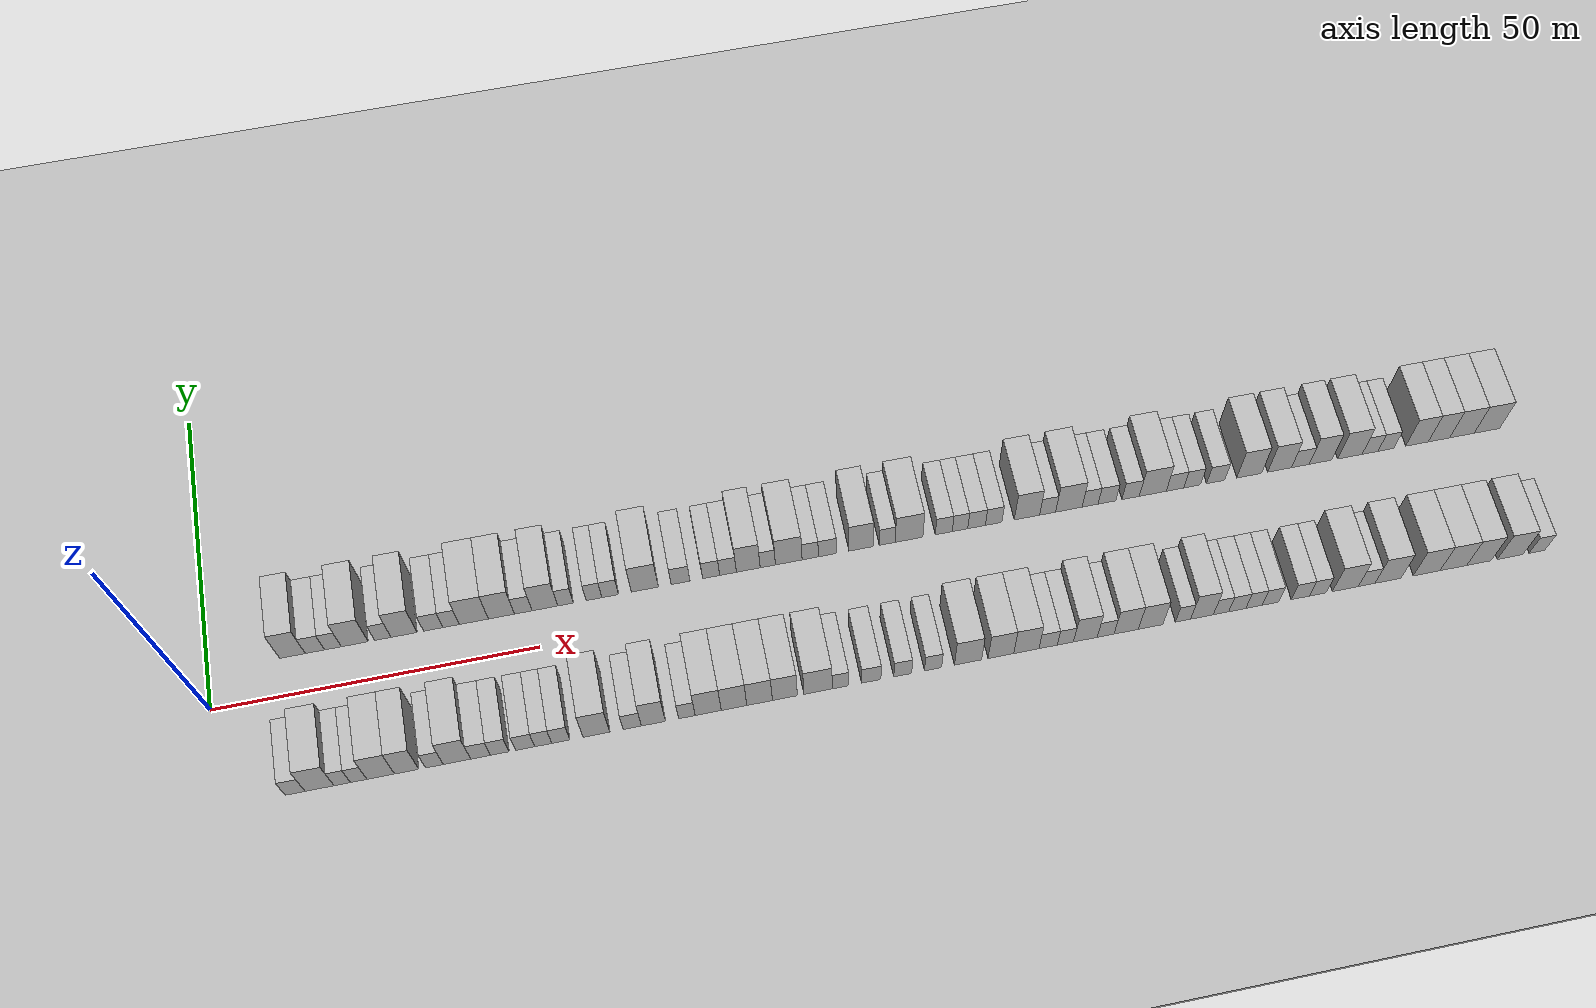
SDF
<?xml version="1.0" encoding="utf-8"?>

<sdf version="1.6">

   <world name="default">

      <gui fullscreen="0">

         <camera name="user_camera">

            <pose>-15 0 4.57585 0 0 0</pose>

            <view_controller>orbit</view_controller>

         </camera>

      </gui>

      <scene>

         <sky>

           <clouds>

             <speed>12</speed>

           </clouds>

         </sky>

         <ambient>0.4 0.4 0.4 1</ambient>

         <background>0.7 0.7 0.7 1</background>

         <shadows>1</shadows>

      </scene>

      <gravity>0 0 -9.8066</gravity>

      <magnetic_field>6e-06 2.3e-05 -4.2e-05</magnetic_field>

      <physics default="0" name="default_physics" type="ode">

         <ode>

            <solver>

               <type>quick</type>

               <iters>10</iters>

               <sor>1.0</sor>

               <use_dynamic_moi_rescaling>0</use_dynamic_moi_rescaling>

            </solver>

            <constraints>

               <cfm>0</cfm>

               <erp>0.2</erp>

               <contact_max_correcting_vel>100</contact_max_correcting_vel>

               <contact_surface_layer>0.001</contact_surface_layer>

            </constraints>

         </ode>

         <max_step_size>0.004</max_step_size>

         <real_time_factor>1</real_time_factor>

         <real_time_update_rate>250</real_time_update_rate>

      </physics>

      <light name="sun" type="directional">

         <cast_shadows>1</cast_shadows>

         <pose>0 0 10 0 0 0</pose>

         <diffuse>0.8 0.8 0.8 1</diffuse>

         <specular>0.2 0.2 0.2 1</specular>

         <attenuation>

            <range>1000</range>

            <constant>0.9</constant>

            <linear>0.01</linear>

            <quadratic>0.001</quadratic>

         </attenuation>

         <direction>-0.5 0.1 -0.9</direction>

      </light>

      <include>

         <name>ground_plane_1</name>

         <uri>model://HANNAS_ground_plane</uri>

         <pose>0 0 0  0 0 0</pose>

      </include>

      <include>

         <name>ground_plane_2</name>

         <uri>model://HANNAS_ground_plane</uri>

         <pose>100 0 0  0 0 0</pose>

      </include>

      <model name="building_1">

         <static>1</static>

         <pose frame="">12.9525 11.0000 0 0.000000 0.000000 1.570796</pose>

         <link name="link">

            <pose frame="">0 0 4.50 0 0 0</pose>

            <collision name="collision">

               <geometry>

                  <box>

                     <size>10.0000 3.9050 9.0000</size>

                  </box>

               </geometry>

               <max_contacts>10</max_contacts>

               <surface>

                  <contact>

                     <ode/>

                  </contact>

                  <bounce/>

                  <friction>

                     <torsional>

                        <ode/>

                     </torsional>

                     <ode/>

                  </friction>

               </surface>

            </collision>

            <visual name="visual">

               <cast_shadows>0</cast_shadows>

               <geometry>

                  <box>

                     <size>10.0000 3.9050 9.0000</size>

                  </box>

               </geometry>

               <material>

                  <script>

                     <uri>model://HANNAS_wall/materials/scripts</uri>

                     <uri>model://HANNAS_wall/materials/textures</uri>

                     <name>vrc/HANNAS_wall</name>

                  </script>

               </material>

            </visual>

            <self_collide>0</self_collide>

            <enable_wind>0</enable_wind>

            <kinematic>0</kinematic>

         </link>

      </model>

      <model name="building_2">

         <static>1</static>

         <pose frame="">16.3775 11.0000 0 0.000000 0.000000 1.570796</pose>

         <link name="link">

            <pose frame="">0 0 3.00 0 0 0</pose>

            <collision name="collision">

               <geometry>

                  <box>

                     <size>10.0000 2.9451 6.0000</size>

                  </box>

               </geometry>

               <max_contacts>10</max_contacts>

               <surface>

                  <contact>

                     <ode/>

                  </contact>

                  <bounce/>

                  <friction>

                     <torsional>

                        <ode/>

                     </torsional>

                     <ode/>

                  </friction>

               </surface>

            </collision>

            <visual name="visual">

               <cast_shadows>0</cast_shadows>

               <geometry>

                  <box>

                     <size>10.0000 2.9451 6.0000</size>

                  </box>

               </geometry>

               <material>

                  <script>

                     <uri>model://HANNAS_wall/materials/scripts</uri>

                     <uri>model://HANNAS_wall/materials/textures</uri>

                     <name>vrc/HANNAS_wall</name>

                  </script>

               </material>

            </visual>

            <self_collide>0</self_collide>

            <enable_wind>0</enable_wind>

            <kinematic>0</kinematic>

         </link>

      </model>

      <model name="building_3">

         <static>1</static>

         <pose frame="">19.1167 11.0000 0 0.000000 0.000000 1.570796</pose>

         <link name="link">

            <pose frame="">0 0 3.00 0 0 0</pose>

            <collision name="collision">

               <geometry>

                  <box>

                     <size>10.0000 2.5333 6.0000</size>

                  </box>

               </geometry>

               <max_contacts>10</max_contacts>

               <surface>

                  <contact>

                     <ode/>

                  </contact>

                  <bounce/>

                  <friction>

                     <torsional>

                        <ode/>

                     </torsional>

                     <ode/>

                  </friction>

               </surface>

            </collision>

            <visual name="visual">

               <cast_shadows>0</cast_shadows>

               <geometry>

                  <box>

                     <size>10.0000 2.5333 6.0000</size>

                  </box>

               </geometry>

               <material>

                  <script>

                     <uri>model://HANNAS_wall/materials/scripts</uri>

                     <uri>model://HANNAS_wall/materials/textures</uri>

                     <name>vrc/HANNAS_wall</name>

                  </script>

               </material>

            </visual>

            <self_collide>0</self_collide>

            <enable_wind>0</enable_wind>

            <kinematic>0</kinematic>

         </link>

      </model>

      <model name="building_4">

         <static>1</static>

         <pose frame="">22.4323 11.0000 0 0.000000 0.000000 1.570796</pose>

         <link name="link">

            <pose frame="">0 0 4.50 0 0 0</pose>

            <collision name="collision">

               <geometry>

                  <box>

                     <size>10.0000 4.0978 9.0000</size>

                  </box>

               </geometry>

               <max_contacts>10</max_contacts>

               <surface>

                  <contact>

                     <ode/>

                  </contact>

                  <bounce/>

                  <friction>

                     <torsional>

                        <ode/>

                     </torsional>

                     <ode/>

                  </friction>

               </surface>

            </collision>

            <visual name="visual">

               <cast_shadows>0</cast_shadows>

               <geometry>

                  <box>

                     <size>10.0000 4.0978 9.0000</size>

                  </box>

               </geometry>

               <material>

                  <script>

                     <uri>model://HANNAS_wall/materials/scripts</uri>

                     <uri>model://HANNAS_wall/materials/textures</uri>

                     <name>vrc/HANNAS_wall</name>

                  </script>

               </material>

            </visual>

            <self_collide>0</self_collide>

            <enable_wind>0</enable_wind>

            <kinematic>0</kinematic>

         </link>

      </model>

      <model name="building_5">

         <static>1</static>

         <pose frame="">26.7356 11.0000 0 0.000000 0.000000 1.570796</pose>

         <link name="link">

            <pose frame="">0 0 3.00 0 0 0</pose>

            <collision name="collision">

               <geometry>

                  <box>

                     <size>10.0000 2.5089 6.0000</size>

                  </box>

               </geometry>

               <max_contacts>10</max_contacts>

               <surface>

                  <contact>

                     <ode/>

                  </contact>

                  <bounce/>

                  <friction>

                     <torsional>

                        <ode/>

                     </torsional>

                     <ode/>

                  </friction>

               </surface>

            </collision>

            <visual name="visual">

               <cast_shadows>0</cast_shadows>

               <geometry>

                  <box>

                     <size>10.0000 2.5089 6.0000</size>

                  </box>

               </geometry>

               <material>

                  <script>

                     <uri>model://HANNAS_wall/materials/scripts</uri>

                     <uri>model://HANNAS_wall/materials/textures</uri>

                     <name>vrc/HANNAS_wall</name>

                  </script>

               </material>

            </visual>

            <self_collide>0</self_collide>

            <enable_wind>0</enable_wind>

            <kinematic>0</kinematic>

         </link>

      </model>

      <model name="building_6">

         <static>1</static>

         <pose frame="">29.9888 11.0000 0 0.000000 0.000000 1.570796</pose>

         <link name="link">

            <pose frame="">0 0 4.50 0 0 0</pose>

            <collision name="collision">

               <geometry>

                  <box>

                     <size>10.0000 3.9976 9.0000</size>

                  </box>

               </geometry>

               <max_contacts>10</max_contacts>

               <surface>

                  <contact>

                     <ode/>

                  </contact>

                  <bounce/>

                  <friction>

                     <torsional>

                        <ode/>

                     </torsional>

                     <ode/>

                  </friction>

               </surface>

            </collision>

            <visual name="visual">

               <cast_shadows>0</cast_shadows>

               <geometry>

                  <box>

                     <size>10.0000 3.9976 9.0000</size>

                  </box>

               </geometry>

               <material>

                  <script>

                     <uri>model://HANNAS_wall/materials/scripts</uri>

                     <uri>model://HANNAS_wall/materials/textures</uri>

                     <name>vrc/HANNAS_wall</name>

                  </script>

               </material>

            </visual>

            <self_collide>0</self_collide>

            <enable_wind>0</enable_wind>

            <kinematic>0</kinematic>

         </link>

      </model>

      <model name="building_7">

         <static>1</static>

         <pose frame="">34.4759 11.0000 0 0.000000 0.000000 1.570796</pose>

         <link name="link">

            <pose frame="">0 0 3.00 0 0 0</pose>

            <collision name="collision">

               <geometry>

                  <box>

                     <size>10.0000 2.9765 6.0000</size>

                  </box>

               </geometry>

               <max_contacts>10</max_contacts>

               <surface>

                  <contact>

                     <ode/>

                  </contact>

                  <bounce/>

                  <friction>

                     <torsional>

                        <ode/>

                     </torsional>

                     <ode/>

                  </friction>

               </surface>

            </collision>

            <visual name="visual">

               <cast_shadows>0</cast_shadows>

               <geometry>

                  <box>

                     <size>10.0000 2.9765 6.0000</size>

                  </box>

               </geometry>

               <material>

                  <script>

                     <uri>model://HANNAS_wall/materials/scripts</uri>

                     <uri>model://HANNAS_wall/materials/textures</uri>

                     <name>vrc/HANNAS_wall</name>

                  </script>

               </material>

            </visual>

            <self_collide>0</self_collide>

            <enable_wind>0</enable_wind>

            <kinematic>0</kinematic>

         </link>

      </model>

      <model name="building_8">

         <static>1</static>

         <pose frame="">37.2237 11.0000 0 0.000000 0.000000 1.570796</pose>

         <link name="link">

            <pose frame="">0 0 3.00 0 0 0</pose>

            <collision name="collision">

               <geometry>

                  <box>

                     <size>10.0000 2.5192 6.0000</size>

                  </box>

               </geometry>

               <max_contacts>10</max_contacts>

               <surface>

                  <contact>

                     <ode/>

                  </contact>

                  <bounce/>

                  <friction>

                     <torsional>

                        <ode/>

                     </torsional>

                     <ode/>

                  </friction>

               </surface>

            </collision>

            <visual name="visual">

               <cast_shadows>0</cast_shadows>

               <geometry>

                  <box>

                     <size>10.0000 2.5192 6.0000</size>

                  </box>

               </geometry>

               <material>

                  <script>

                     <uri>model://HANNAS_wall/materials/scripts</uri>

                     <uri>model://HANNAS_wall/materials/textures</uri>

                     <name>vrc/HANNAS_wall</name>

                  </script>

               </material>

            </visual>

            <self_collide>0</self_collide>

            <enable_wind>0</enable_wind>

            <kinematic>0</kinematic>

         </link>

      </model>

      <model name="building_9">

         <static>1</static>

         <pose frame="">40.7293 11.0000 0 0.000000 0.000000 1.570796</pose>

         <link name="link">

            <pose frame="">0 0 4.50 0 0 0</pose>

            <collision name="collision">

               <geometry>

                  <box>

                     <size>10.0000 4.4920 9.0000</size>

                  </box>

               </geometry>

               <max_contacts>10</max_contacts>

               <surface>

                  <contact>

                     <ode/>

                  </contact>

                  <bounce/>

                  <friction>

                     <torsional>

                        <ode/>

                     </torsional>

                     <ode/>

                  </friction>

               </surface>

            </collision>

            <visual name="visual">

               <cast_shadows>0</cast_shadows>

               <geometry>

                  <box>

                     <size>10.0000 4.4920 9.0000</size>

                  </box>

               </geometry>

               <material>

                  <script>

                     <uri>model://HANNAS_wall/materials/scripts</uri>

                     <uri>model://HANNAS_wall/materials/textures</uri>

                     <name>vrc/HANNAS_wall</name>

                  </script>

               </material>

            </visual>

            <self_collide>0</self_collide>

            <enable_wind>0</enable_wind>

            <kinematic>0</kinematic>

         </link>

      </model>

      <model name="building_10">

         <static>1</static>

         <pose frame="">44.9919 11.0000 0 0.000000 0.000000 1.570796</pose>

         <link name="link">

            <pose frame="">0 0 4.50 0 0 0</pose>

            <collision name="collision">

               <geometry>

                  <box>

                     <size>10.0000 4.0332 9.0000</size>

                  </box>

               </geometry>

               <max_contacts>10</max_contacts>

               <surface>

                  <contact>

                     <ode/>

                  </contact>

                  <bounce/>

                  <friction>

                     <torsional>

                        <ode/>

                     </torsional>

                     <ode/>

                  </friction>

               </surface>

            </collision>

            <visual name="visual">

               <cast_shadows>0</cast_shadows>

               <geometry>

                  <box>

                     <size>10.0000 4.0332 9.0000</size>

                  </box>

               </geometry>

               <material>

                  <script>

                     <uri>model://HANNAS_wall/materials/scripts</uri>

                     <uri>model://HANNAS_wall/materials/textures</uri>

                     <name>vrc/HANNAS_wall</name>

                  </script>

               </material>

            </visual>

            <self_collide>0</self_collide>

            <enable_wind>0</enable_wind>

            <kinematic>0</kinematic>

         </link>

      </model>

      <model name="building_11">

         <static>1</static>

         <pose frame="">48.3769 11.0000 0 0.000000 0.000000 1.570796</pose>

         <link name="link">

            <pose frame="">0 0 3.00 0 0 0</pose>

            <collision name="collision">

               <geometry>

                  <box>

                     <size>10.0000 2.7368 6.0000</size>

                  </box>

               </geometry>

               <max_contacts>10</max_contacts>

               <surface>

                  <contact>

                     <ode/>

                  </contact>

                  <bounce/>

                  <friction>

                     <torsional>

                        <ode/>

                     </torsional>

                     <ode/>

                  </friction>

               </surface>

            </collision>

            <visual name="visual">

               <cast_shadows>0</cast_shadows>

               <geometry>

                  <box>

                     <size>10.0000 2.7368 6.0000</size>

                  </box>

               </geometry>

               <material>

                  <script>

                     <uri>model://HANNAS_wall/materials/scripts</uri>

                     <uri>model://HANNAS_wall/materials/textures</uri>

                     <name>vrc/HANNAS_wall</name>

                  </script>

               </material>

            </visual>

            <self_collide>0</self_collide>

            <enable_wind>0</enable_wind>

            <kinematic>0</kinematic>

         </link>

      </model>

      <model name="building_12">

         <static>1</static>

         <pose frame="">51.7380 11.0000 0 0.000000 0.000000 1.570796</pose>

         <link name="link">

            <pose frame="">0 0 4.50 0 0 0</pose>

            <collision name="collision">

               <geometry>

                  <box>

                     <size>10.0000 3.9854 9.0000</size>

                  </box>

               </geometry>

               <max_contacts>10</max_contacts>

               <surface>

                  <contact>

                     <ode/>

                  </contact>

                  <bounce/>

                  <friction>

                     <torsional>

                        <ode/>

                     </torsional>

                     <ode/>

                  </friction>

               </surface>

            </collision>

            <visual name="visual">

               <cast_shadows>0</cast_shadows>

               <geometry>

                  <box>

                     <size>10.0000 3.9854 9.0000</size>

                  </box>

               </geometry>

               <material>

                  <script>

                     <uri>model://HANNAS_wall/materials/scripts</uri>

                     <uri>model://HANNAS_wall/materials/textures</uri>

                     <name>vrc/HANNAS_wall</name>

                  </script>

               </material>

            </visual>

            <self_collide>0</self_collide>

            <enable_wind>0</enable_wind>

            <kinematic>0</kinematic>

         </link>

      </model>

      <model name="building_13">

         <static>1</static>

         <pose frame="">54.9431 11.0000 0 0.000000 0.000000 1.570796</pose>

         <link name="link">

            <pose frame="">0 0 3.00 0 0 0</pose>

            <collision name="collision">

               <geometry>

                  <box>

                     <size>10.0000 2.4248 6.0000</size>

                  </box>

               </geometry>

               <max_contacts>10</max_contacts>

               <surface>

                  <contact>

                     <ode/>

                  </contact>

                  <bounce/>

                  <friction>

                     <torsional>

                        <ode/>

                     </torsional>

                     <ode/>

                  </friction>

               </surface>

            </collision>

            <visual name="visual">

               <cast_shadows>0</cast_shadows>

               <geometry>

                  <box>

                     <size>10.0000 2.4248 6.0000</size>

                  </box>

               </geometry>

               <material>

                  <script>

                     <uri>model://HANNAS_wall/materials/scripts</uri>

                     <uri>model://HANNAS_wall/materials/textures</uri>

                     <name>vrc/HANNAS_wall</name>

                  </script>

               </material>

            </visual>

            <self_collide>0</self_collide>

            <enable_wind>0</enable_wind>

            <kinematic>0</kinematic>

         </link>

      </model>

      <model name="building_14">

         <static>1</static>

         <pose frame="">59.3850 11.0000 0 0.000000 0.000000 1.570796</pose>

         <link name="link">

            <pose frame="">0 0 3.00 0 0 0</pose>

            <collision name="collision">

               <geometry>

                  <box>

                     <size>10.0000 2.4591 6.0000</size>

                  </box>

               </geometry>

               <max_contacts>10</max_contacts>

               <surface>

                  <contact>

                     <ode/>

                  </contact>

                  <bounce/>

                  <friction>

                     <torsional>

                        <ode/>

                     </torsional>

                     <ode/>

                  </friction>

               </surface>

            </collision>

            <visual name="visual">

               <cast_shadows>0</cast_shadows>

               <geometry>

                  <box>

                     <size>10.0000 2.4591 6.0000</size>

                  </box>

               </geometry>

               <material>

                  <script>

                     <uri>model://HANNAS_wall/materials/scripts</uri>

                     <uri>model://HANNAS_wall/materials/textures</uri>

                     <name>vrc/HANNAS_wall</name>

                  </script>

               </material>

            </visual>

            <self_collide>0</self_collide>

            <enable_wind>0</enable_wind>

            <kinematic>0</kinematic>

         </link>

      </model>

      <model name="building_15">

         <static>1</static>

         <pose frame="">61.9111 11.0000 0 0.000000 0.000000 1.570796</pose>

         <link name="link">

            <pose frame="">0 0 3.00 0 0 0</pose>

            <collision name="collision">

               <geometry>

                  <box>

                     <size>10.0000 2.5931 6.0000</size>

                  </box>

               </geometry>

               <max_contacts>10</max_contacts>

               <surface>

                  <contact>

                     <ode/>

                  </contact>

                  <bounce/>

                  <friction>

                     <torsional>

                        <ode/>

                     </torsional>

                     <ode/>

                  </friction>

               </surface>

            </collision>

            <visual name="visual">

               <cast_shadows>0</cast_shadows>

               <geometry>

                  <box>

                     <size>10.0000 2.5931 6.0000</size>

                  </box>

               </geometry>

               <material>

                  <script>

                     <uri>model://HANNAS_wall/materials/scripts</uri>

                     <uri>model://HANNAS_wall/materials/textures</uri>

                     <name>vrc/HANNAS_wall</name>

                  </script>

               </material>

            </visual>

            <self_collide>0</self_collide>

            <enable_wind>0</enable_wind>

            <kinematic>0</kinematic>

         </link>

      </model>

      <model name="building_16">

         <static>1</static>

         <pose frame="">67.3301 11.0000 0 0.000000 0.000000 1.570796</pose>

         <link name="link">

            <pose frame="">0 0 4.50 0 0 0</pose>

            <collision name="collision">

               <geometry>

                  <box>

                     <size>10.0000 4.2447 9.0000</size>

                  </box>

               </geometry>

               <max_contacts>10</max_contacts>

               <surface>

                  <contact>

                     <ode/>

                  </contact>

                  <bounce/>

                  <friction>

                     <torsional>

                        <ode/>

                     </torsional>

                     <ode/>

                  </friction>

               </surface>

            </collision>

            <visual name="visual">

               <cast_shadows>0</cast_shadows>

               <geometry>

                  <box>

                     <size>10.0000 4.2447 9.0000</size>

                  </box>

               </geometry>

               <material>

                  <script>

                     <uri>model://HANNAS_wall/materials/scripts</uri>

                     <uri>model://HANNAS_wall/materials/textures</uri>

                     <name>vrc/HANNAS_wall</name>

                  </script>

               </material>

            </visual>

            <self_collide>0</self_collide>

            <enable_wind>0</enable_wind>

            <kinematic>0</kinematic>

         </link>

      </model>

      <model name="building_17">

         <static>1</static>

         <pose frame="">72.9326 11.0000 0 0.000000 0.000000 1.570796</pose>

         <link name="link">

            <pose frame="">0 0 3.00 0 0 0</pose>

            <collision name="collision">

               <geometry>

                  <box>

                     <size>10.0000 2.9604 6.0000</size>

                  </box>

               </geometry>

               <max_contacts>10</max_contacts>

               <surface>

                  <contact>

                     <ode/>

                  </contact>

                  <bounce/>

                  <friction>

                     <torsional>

                        <ode/>

                     </torsional>

                     <ode/>

                  </friction>

               </surface>

            </collision>

            <visual name="visual">

               <cast_shadows>0</cast_shadows>

               <geometry>

                  <box>

                     <size>10.0000 2.9604 6.0000</size>

                  </box>

               </geometry>

               <material>

                  <script>

                     <uri>model://HANNAS_wall/materials/scripts</uri>

                     <uri>model://HANNAS_wall/materials/textures</uri>

                     <name>vrc/HANNAS_wall</name>

                  </script>

               </material>

            </visual>

            <self_collide>0</self_collide>

            <enable_wind>0</enable_wind>

            <kinematic>0</kinematic>

         </link>

      </model>

      <model name="building_18">

         <static>1</static>

         <pose frame="">77.7498 11.0000 0 0.000000 0.000000 1.570796</pose>

         <link name="link">

            <pose frame="">0 0 3.00 0 0 0</pose>

            <collision name="collision">

               <geometry>

                  <box>

                     <size>10.0000 2.6740 6.0000</size>

                  </box>

               </geometry>

               <max_contacts>10</max_contacts>

               <surface>

                  <contact>

                     <ode/>

                  </contact>

                  <bounce/>

                  <friction>

                     <torsional>

                        <ode/>

                     </torsional>

                     <ode/>

                  </friction>

               </surface>

            </collision>

            <visual name="visual">

               <cast_shadows>0</cast_shadows>

               <geometry>

                  <box>

                     <size>10.0000 2.6740 6.0000</size>

                  </box>

               </geometry>

               <material>

                  <script>

                     <uri>model://HANNAS_wall/materials/scripts</uri>

                     <uri>model://HANNAS_wall/materials/textures</uri>

                     <name>vrc/HANNAS_wall</name>

                  </script>

               </material>

            </visual>

            <self_collide>0</self_collide>

            <enable_wind>0</enable_wind>

            <kinematic>0</kinematic>

         </link>

      </model>

      <model name="building_19">

         <static>1</static>

         <pose frame="">80.4077 11.0000 0 0.000000 0.000000 1.570796</pose>

         <link name="link">

            <pose frame="">0 0 3.00 0 0 0</pose>

            <collision name="collision">

               <geometry>

                  <box>

                     <size>10.0000 2.6417 6.0000</size>

                  </box>

               </geometry>

               <max_contacts>10</max_contacts>

               <surface>

                  <contact>

                     <ode/>

                  </contact>

                  <bounce/>

                  <friction>

                     <torsional>

                        <ode/>

                     </torsional>

                     <ode/>

                  </friction>

               </surface>

            </collision>

            <visual name="visual">

               <cast_shadows>0</cast_shadows>

               <geometry>

                  <box>

                     <size>10.0000 2.6417 6.0000</size>

                  </box>

               </geometry>

               <material>

                  <script>

                     <uri>model://HANNAS_wall/materials/scripts</uri>

                     <uri>model://HANNAS_wall/materials/textures</uri>

                     <name>vrc/HANNAS_wall</name>

                  </script>

               </material>

            </visual>

            <self_collide>0</self_collide>

            <enable_wind>0</enable_wind>

            <kinematic>0</kinematic>

         </link>

      </model>

      <model name="building_20">

         <static>1</static>

         <pose frame="">83.6070 11.0000 0 0.000000 0.000000 1.570796</pose>

         <link name="link">

            <pose frame="">0 0 4.50 0 0 0</pose>

            <collision name="collision">

               <geometry>

                  <box>

                     <size>10.0000 3.7568 9.0000</size>

                  </box>

               </geometry>

               <max_contacts>10</max_contacts>

               <surface>

                  <contact>

                     <ode/>

                  </contact>

                  <bounce/>

                  <friction>

                     <torsional>

                        <ode/>

                     </torsional>

                     <ode/>

                  </friction>

               </surface>

            </collision>

            <visual name="visual">

               <cast_shadows>0</cast_shadows>

               <geometry>

                  <box>

                     <size>10.0000 3.7568 9.0000</size>

                  </box>

               </geometry>

               <material>

                  <script>

                     <uri>model://HANNAS_wall/materials/scripts</uri>

                     <uri>model://HANNAS_wall/materials/textures</uri>

                     <name>vrc/HANNAS_wall</name>

                  </script>

               </material>

            </visual>

            <self_collide>0</self_collide>

            <enable_wind>0</enable_wind>

            <kinematic>0</kinematic>

         </link>

      </model>

      <model name="building_21">

         <static>1</static>

         <pose frame="">86.6971 11.0000 0 0.000000 0.000000 1.570796</pose>

         <link name="link">

            <pose frame="">0 0 3.00 0 0 0</pose>

            <collision name="collision">

               <geometry>

                  <box>

                     <size>10.0000 2.4235 6.0000</size>

                  </box>

               </geometry>

               <max_contacts>10</max_contacts>

               <surface>

                  <contact>

                     <ode/>

                  </contact>

                  <bounce/>

                  <friction>

                     <torsional>

                        <ode/>

                     </torsional>

                     <ode/>

                  </friction>

               </surface>

            </collision>

            <visual name="visual">

               <cast_shadows>0</cast_shadows>

               <geometry>

                  <box>

                     <size>10.0000 2.4235 6.0000</size>

                  </box>

               </geometry>

               <material>

                  <script>

                     <uri>model://HANNAS_wall/materials/scripts</uri>

                     <uri>model://HANNAS_wall/materials/textures</uri>

                     <name>vrc/HANNAS_wall</name>

                  </script>

               </material>

            </visual>

            <self_collide>0</self_collide>

            <enable_wind>0</enable_wind>

            <kinematic>0</kinematic>

         </link>

      </model>

      <model name="building_22">

         <static>1</static>

         <pose frame="">90.0248 11.0000 0 0.000000 0.000000 1.570796</pose>

         <link name="link">

            <pose frame="">0 0 4.50 0 0 0</pose>

            <collision name="collision">

               <geometry>

                  <box>

                     <size>10.0000 4.2320 9.0000</size>

                  </box>

               </geometry>

               <max_contacts>10</max_contacts>

               <surface>

                  <contact>

                     <ode/>

                  </contact>

                  <bounce/>

                  <friction>

                     <torsional>

                        <ode/>

                     </torsional>

                     <ode/>

                  </friction>

               </surface>

            </collision>

            <visual name="visual">

               <cast_shadows>0</cast_shadows>

               <geometry>

                  <box>

                     <size>10.0000 4.2320 9.0000</size>

                  </box>

               </geometry>

               <material>

                  <script>

                     <uri>model://HANNAS_wall/materials/scripts</uri>

                     <uri>model://HANNAS_wall/materials/textures</uri>

                     <name>vrc/HANNAS_wall</name>

                  </script>

               </material>

            </visual>

            <self_collide>0</self_collide>

            <enable_wind>0</enable_wind>

            <kinematic>0</kinematic>

         </link>

      </model>

      <model name="building_23">

         <static>1</static>

         <pose frame="">93.4346 11.0000 0 0.000000 0.000000 1.570796</pose>

         <link name="link">

            <pose frame="">0 0 3.00 0 0 0</pose>

            <collision name="collision">

               <geometry>

                  <box>

                     <size>10.0000 2.5876 6.0000</size>

                  </box>

               </geometry>

               <max_contacts>10</max_contacts>

               <surface>

                  <contact>

                     <ode/>

                  </contact>

                  <bounce/>

                  <friction>

                     <torsional>

                        <ode/>

                     </torsional>

                     <ode/>

                  </friction>

               </surface>

            </collision>

            <visual name="visual">

               <cast_shadows>0</cast_shadows>

               <geometry>

                  <box>

                     <size>10.0000 2.5876 6.0000</size>

                  </box>

               </geometry>

               <material>

                  <script>

                     <uri>model://HANNAS_wall/materials/scripts</uri>

                     <uri>model://HANNAS_wall/materials/textures</uri>

                     <name>vrc/HANNAS_wall</name>

                  </script>

               </material>

            </visual>

            <self_collide>0</self_collide>

            <enable_wind>0</enable_wind>

            <kinematic>0</kinematic>

         </link>

      </model>

      <model name="building_24">

         <static>1</static>

         <pose frame="">96.1664 11.0000 0 0.000000 0.000000 1.570796</pose>

         <link name="link">

            <pose frame="">0 0 3.00 0 0 0</pose>

            <collision name="collision">

               <geometry>

                  <box>

                     <size>10.0000 2.8760 6.0000</size>

                  </box>

               </geometry>

               <max_contacts>10</max_contacts>

               <surface>

                  <contact>

                     <ode/>

                  </contact>

                  <bounce/>

                  <friction>

                     <torsional>

                        <ode/>

                     </torsional>

                     <ode/>

                  </friction>

               </surface>

            </collision>

            <visual name="visual">

               <cast_shadows>0</cast_shadows>

               <geometry>

                  <box>

                     <size>10.0000 2.8760 6.0000</size>

                  </box>

               </geometry>

               <material>

                  <script>

                     <uri>model://HANNAS_wall/materials/scripts</uri>

                     <uri>model://HANNAS_wall/materials/textures</uri>

                     <name>vrc/HANNAS_wall</name>

                  </script>

               </material>

            </visual>

            <self_collide>0</self_collide>

            <enable_wind>0</enable_wind>

            <kinematic>0</kinematic>

         </link>

      </model>

      <model name="building_25">

         <static>1</static>

         <pose frame="">101.5281 11.0000 0 0.000000 0.000000 1.570796</pose>

         <link name="link">

            <pose frame="">0 0 4.50 0 0 0</pose>

            <collision name="collision">

               <geometry>

                  <box>

                     <size>10.0000 3.8472 9.0000</size>

                  </box>

               </geometry>

               <max_contacts>10</max_contacts>

               <surface>

                  <contact>

                     <ode/>

                  </contact>

                  <bounce/>

                  <friction>

                     <torsional>

                        <ode/>

                     </torsional>

                     <ode/>

                  </friction>

               </surface>

            </collision>

            <visual name="visual">

               <cast_shadows>0</cast_shadows>

               <geometry>

                  <box>

                     <size>10.0000 3.8472 9.0000</size>

                  </box>

               </geometry>

               <material>

                  <script>

                     <uri>model://HANNAS_wall/materials/scripts</uri>

                     <uri>model://HANNAS_wall/materials/textures</uri>

                     <name>vrc/HANNAS_wall</name>

                  </script>

               </material>

            </visual>

            <self_collide>0</self_collide>

            <enable_wind>0</enable_wind>

            <kinematic>0</kinematic>

         </link>

      </model>

      <model name="building_26">

         <static>1</static>

         <pose frame="">105.7245 11.0000 0 0.000000 0.000000 1.570796</pose>

         <link name="link">

            <pose frame="">0 0 3.00 0 0 0</pose>

            <collision name="collision">

               <geometry>

                  <box>

                     <size>10.0000 2.5457 6.0000</size>

                  </box>

               </geometry>

               <max_contacts>10</max_contacts>

               <surface>

                  <contact>

                     <ode/>

                  </contact>

                  <bounce/>

                  <friction>

                     <torsional>

                        <ode/>

                     </torsional>

                     <ode/>

                  </friction>

               </surface>

            </collision>

            <visual name="visual">

               <cast_shadows>0</cast_shadows>

               <geometry>

                  <box>

                     <size>10.0000 2.5457 6.0000</size>

                  </box>

               </geometry>

               <material>

                  <script>

                     <uri>model://HANNAS_wall/materials/scripts</uri>

                     <uri>model://HANNAS_wall/materials/textures</uri>

                     <name>vrc/HANNAS_wall</name>

                  </script>

               </material>

            </visual>

            <self_collide>0</self_collide>

            <enable_wind>0</enable_wind>

            <kinematic>0</kinematic>

         </link>

      </model>

      <model name="building_27">

         <static>1</static>

         <pose frame="">109.2187 11.0000 0 0.000000 0.000000 1.570796</pose>

         <link name="link">

            <pose frame="">0 0 4.50 0 0 0</pose>

            <collision name="collision">

               <geometry>

                  <box>

                     <size>10.0000 4.4427 9.0000</size>

                  </box>

               </geometry>

               <max_contacts>10</max_contacts>

               <surface>

                  <contact>

                     <ode/>

                  </contact>

                  <bounce/>

                  <friction>

                     <torsional>

                        <ode/>

                     </torsional>

                     <ode/>

                  </friction>

               </surface>

            </collision>

            <visual name="visual">

               <cast_shadows>0</cast_shadows>

               <geometry>

                  <box>

                     <size>10.0000 4.4427 9.0000</size>

                  </box>

               </geometry>

               <material>

                  <script>

                     <uri>model://HANNAS_wall/materials/scripts</uri>

                     <uri>model://HANNAS_wall/materials/textures</uri>

                     <name>vrc/HANNAS_wall</name>

                  </script>

               </material>

            </visual>

            <self_collide>0</self_collide>

            <enable_wind>0</enable_wind>

            <kinematic>0</kinematic>

         </link>

      </model>

      <model name="building_28">

         <static>1</static>

         <pose frame="">114.8032 11.0000 0 0.000000 0.000000 1.570796</pose>

         <link name="link">

            <pose frame="">0 0 3.00 0 0 0</pose>

            <collision name="collision">

               <geometry>

                  <box>

                     <size>10.0000 2.7262 6.0000</size>

                  </box>

               </geometry>

               <max_contacts>10</max_contacts>

               <surface>

                  <contact>

                     <ode/>

                  </contact>

                  <bounce/>

                  <friction>

                     <torsional>

                        <ode/>

                     </torsional>

                     <ode/>

                  </friction>

               </surface>

            </collision>

            <visual name="visual">

               <cast_shadows>0</cast_shadows>

               <geometry>

                  <box>

                     <size>10.0000 2.7262 6.0000</size>

                  </box>

               </geometry>

               <material>

                  <script>

                     <uri>model://HANNAS_wall/materials/scripts</uri>

                     <uri>model://HANNAS_wall/materials/textures</uri>

                     <name>vrc/HANNAS_wall</name>

                  </script>

               </material>

            </visual>

            <self_collide>0</self_collide>

            <enable_wind>0</enable_wind>

            <kinematic>0</kinematic>

         </link>

      </model>

      <model name="building_29">

         <static>1</static>

         <pose frame="">117.4157 11.0000 0 0.000000 0.000000 1.570796</pose>

         <link name="link">

            <pose frame="">0 0 3.00 0 0 0</pose>

            <collision name="collision">

               <geometry>

                  <box>

                     <size>10.0000 2.4989 6.0000</size>

                  </box>

               </geometry>

               <max_contacts>10</max_contacts>

               <surface>

                  <contact>

                     <ode/>

                  </contact>

                  <bounce/>

                  <friction>

                     <torsional>

                        <ode/>

                     </torsional>

                     <ode/>

                  </friction>

               </surface>

            </collision>

            <visual name="visual">

               <cast_shadows>0</cast_shadows>

               <geometry>

                  <box>

                     <size>10.0000 2.4989 6.0000</size>

                  </box>

               </geometry>

               <material>

                  <script>

                     <uri>model://HANNAS_wall/materials/scripts</uri>

                     <uri>model://HANNAS_wall/materials/textures</uri>

                     <name>vrc/HANNAS_wall</name>

                  </script>

               </material>

            </visual>

            <self_collide>0</self_collide>

            <enable_wind>0</enable_wind>

            <kinematic>0</kinematic>

         </link>

      </model>

      <model name="building_30">

         <static>1</static>

         <pose frame="">120.0866 11.0000 0 0.000000 0.000000 1.570796</pose>

         <link name="link">

            <pose frame="">0 0 3.00 0 0 0</pose>

            <collision name="collision">

               <geometry>

                  <box>

                     <size>10.0000 2.8430 6.0000</size>

                  </box>

               </geometry>

               <max_contacts>10</max_contacts>

               <surface>

                  <contact>

                     <ode/>

                  </contact>

                  <bounce/>

                  <friction>

                     <torsional>

                        <ode/>

                     </torsional>

                     <ode/>

                  </friction>

               </surface>

            </collision>

            <visual name="visual">

               <cast_shadows>0</cast_shadows>

               <geometry>

                  <box>

                     <size>10.0000 2.8430 6.0000</size>

                  </box>

               </geometry>

               <material>

                  <script>

                     <uri>model://HANNAS_wall/materials/scripts</uri>

                     <uri>model://HANNAS_wall/materials/textures</uri>

                     <name>vrc/HANNAS_wall</name>

                  </script>

               </material>

            </visual>

            <self_collide>0</self_collide>

            <enable_wind>0</enable_wind>

            <kinematic>0</kinematic>

         </link>

      </model>

      <model name="building_31">

         <static>1</static>

         <pose frame="">122.8462 11.0000 0 0.000000 0.000000 1.570796</pose>

         <link name="link">

            <pose frame="">0 0 3.00 0 0 0</pose>

            <collision name="collision">

               <geometry>

                  <box>

                     <size>10.0000 2.6762 6.0000</size>

                  </box>

               </geometry>

               <max_contacts>10</max_contacts>

               <surface>

                  <contact>

                     <ode/>

                  </contact>

                  <bounce/>

                  <friction>

                     <torsional>

                        <ode/>

                     </torsional>

                     <ode/>

                  </friction>

               </surface>

            </collision>

            <visual name="visual">

               <cast_shadows>0</cast_shadows>

               <geometry>

                  <box>

                     <size>10.0000 2.6762 6.0000</size>

                  </box>

               </geometry>

               <material>

                  <script>

                     <uri>model://HANNAS_wall/materials/scripts</uri>

                     <uri>model://HANNAS_wall/materials/textures</uri>

                     <name>vrc/HANNAS_wall</name>

                  </script>

               </material>

            </visual>

            <self_collide>0</self_collide>

            <enable_wind>0</enable_wind>

            <kinematic>0</kinematic>

         </link>

      </model>

      <model name="building_32">

         <static>1</static>

         <pose frame="">128.2343 11.0000 0 0.000000 0.000000 1.570796</pose>

         <link name="link">

            <pose frame="">0 0 4.50 0 0 0</pose>

            <collision name="collision">

               <geometry>

                  <box>

                     <size>10.0000 4.0998 9.0000</size>

                  </box>

               </geometry>

               <max_contacts>10</max_contacts>

               <surface>

                  <contact>

                     <ode/>

                  </contact>

                  <bounce/>

                  <friction>

                     <torsional>

                        <ode/>

                     </torsional>

                     <ode/>

                  </friction>

               </surface>

            </collision>

            <visual name="visual">

               <cast_shadows>0</cast_shadows>

               <geometry>

                  <box>

                     <size>10.0000 4.0998 9.0000</size>

                  </box>

               </geometry>

               <material>

                  <script>

                     <uri>model://HANNAS_wall/materials/scripts</uri>

                     <uri>model://HANNAS_wall/materials/textures</uri>

                     <name>vrc/HANNAS_wall</name>

                  </script>

               </material>

            </visual>

            <self_collide>0</self_collide>

            <enable_wind>0</enable_wind>

            <kinematic>0</kinematic>

         </link>

      </model>

      <model name="building_33">

         <static>1</static>

         <pose frame="">131.5892 11.0000 0 0.000000 0.000000 1.570796</pose>

         <link name="link">

            <pose frame="">0 0 3.00 0 0 0</pose>

            <collision name="collision">

               <geometry>

                  <box>

                     <size>10.0000 2.6101 6.0000</size>

                  </box>

               </geometry>

               <max_contacts>10</max_contacts>

               <surface>

                  <contact>

                     <ode/>

                  </contact>

                  <bounce/>

                  <friction>

                     <torsional>

                        <ode/>

                     </torsional>

                     <ode/>

                  </friction>

               </surface>

            </collision>

            <visual name="visual">

               <cast_shadows>0</cast_shadows>

               <geometry>

                  <box>

                     <size>10.0000 2.6101 6.0000</size>

                  </box>

               </geometry>

               <material>

                  <script>

                     <uri>model://HANNAS_wall/materials/scripts</uri>

                     <uri>model://HANNAS_wall/materials/textures</uri>

                     <name>vrc/HANNAS_wall</name>

                  </script>

               </material>

            </visual>

            <self_collide>0</self_collide>

            <enable_wind>0</enable_wind>

            <kinematic>0</kinematic>

         </link>

      </model>

      <model name="building_34">

         <static>1</static>

         <pose frame="">135.0570 11.0000 0 0.000000 0.000000 1.570796</pose>

         <link name="link">

            <pose frame="">0 0 4.50 0 0 0</pose>

            <collision name="collision">

               <geometry>

                  <box>

                     <size>10.0000 4.3254 9.0000</size>

                  </box>

               </geometry>

               <max_contacts>10</max_contacts>

               <surface>

                  <contact>

                     <ode/>

                  </contact>

                  <bounce/>

                  <friction>

                     <torsional>

                        <ode/>

                     </torsional>

                     <ode/>

                  </friction>

               </surface>

            </collision>

            <visual name="visual">

               <cast_shadows>0</cast_shadows>

               <geometry>

                  <box>

                     <size>10.0000 4.3254 9.0000</size>

                  </box>

               </geometry>

               <material>

                  <script>

                     <uri>model://HANNAS_wall/materials/scripts</uri>

                     <uri>model://HANNAS_wall/materials/textures</uri>

                     <name>vrc/HANNAS_wall</name>

                  </script>

               </material>

            </visual>

            <self_collide>0</self_collide>

            <enable_wind>0</enable_wind>

            <kinematic>0</kinematic>

         </link>

      </model>

      <model name="building_35">

         <static>1</static>

         <pose frame="">138.5152 11.0000 0 0.000000 0.000000 1.570796</pose>

         <link name="link">

            <pose frame="">0 0 3.00 0 0 0</pose>

            <collision name="collision">

               <geometry>

                  <box>

                     <size>10.0000 2.5910 6.0000</size>

                  </box>

               </geometry>

               <max_contacts>10</max_contacts>

               <surface>

                  <contact>

                     <ode/>

                  </contact>

                  <bounce/>

                  <friction>

                     <torsional>

                        <ode/>

                     </torsional>

                     <ode/>

                  </friction>

               </surface>

            </collision>

            <visual name="visual">

               <cast_shadows>0</cast_shadows>

               <geometry>

                  <box>

                     <size>10.0000 2.5910 6.0000</size>

                  </box>

               </geometry>

               <material>

                  <script>

                     <uri>model://HANNAS_wall/materials/scripts</uri>

                     <uri>model://HANNAS_wall/materials/textures</uri>

                     <name>vrc/HANNAS_wall</name>

                  </script>

               </material>

            </visual>

            <self_collide>0</self_collide>

            <enable_wind>0</enable_wind>

            <kinematic>0</kinematic>

         </link>

      </model>

      <model name="building_36">

         <static>1</static>

         <pose frame="">141.2565 11.0000 0 0.000000 0.000000 1.570796</pose>

         <link name="link">

            <pose frame="">0 0 3.00 0 0 0</pose>

            <collision name="collision">

               <geometry>

                  <box>

                     <size>10.0000 2.8916 6.0000</size>

                  </box>

               </geometry>

               <max_contacts>10</max_contacts>

               <surface>

                  <contact>

                     <ode/>

                  </contact>

                  <bounce/>

                  <friction>

                     <torsional>

                        <ode/>

                     </torsional>

                     <ode/>

                  </friction>

               </surface>

            </collision>

            <visual name="visual">

               <cast_shadows>0</cast_shadows>

               <geometry>

                  <box>

                     <size>10.0000 2.8916 6.0000</size>

                  </box>

               </geometry>

               <material>

                  <script>

                     <uri>model://HANNAS_wall/materials/scripts</uri>

                     <uri>model://HANNAS_wall/materials/textures</uri>

                     <name>vrc/HANNAS_wall</name>

                  </script>

               </material>

            </visual>

            <self_collide>0</self_collide>

            <enable_wind>0</enable_wind>

            <kinematic>0</kinematic>

         </link>

      </model>

      <model name="building_37">

         <static>1</static>

         <pose frame="">145.1205 11.0000 0 0.000000 0.000000 1.570796</pose>

         <link name="link">

            <pose frame="">0 0 3.00 0 0 0</pose>

            <collision name="collision">

               <geometry>

                  <box>

                     <size>10.0000 2.8364 6.0000</size>

                  </box>

               </geometry>

               <max_contacts>10</max_contacts>

               <surface>

                  <contact>

                     <ode/>

                  </contact>

                  <bounce/>

                  <friction>

                     <torsional>

                        <ode/>

                     </torsional>

                     <ode/>

                  </friction>

               </surface>

            </collision>

            <visual name="visual">

               <cast_shadows>0</cast_shadows>

               <geometry>

                  <box>

                     <size>10.0000 2.8364 6.0000</size>

                  </box>

               </geometry>

               <material>

                  <script>

                     <uri>model://HANNAS_wall/materials/scripts</uri>

                     <uri>model://HANNAS_wall/materials/textures</uri>

                     <name>vrc/HANNAS_wall</name>

                  </script>

               </material>

            </visual>

            <self_collide>0</self_collide>

            <enable_wind>0</enable_wind>

            <kinematic>0</kinematic>

         </link>

      </model>

      <model name="building_38">

         <static>1</static>

         <pose frame="">148.7555 11.0000 0 0.000000 0.000000 1.570796</pose>

         <link name="link">

            <pose frame="">0 0 4.50 0 0 0</pose>

            <collision name="collision">

               <geometry>

                  <box>

                     <size>10.0000 4.4335 9.0000</size>

                  </box>

               </geometry>

               <max_contacts>10</max_contacts>

               <surface>

                  <contact>

                     <ode/>

                  </contact>

                  <bounce/>

                  <friction>

                     <torsional>

                        <ode/>

                     </torsional>

                     <ode/>

                  </friction>

               </surface>

            </collision>

            <visual name="visual">

               <cast_shadows>0</cast_shadows>

               <geometry>

                  <box>

                     <size>10.0000 4.4335 9.0000</size>

                  </box>

               </geometry>

               <material>

                  <script>

                     <uri>model://HANNAS_wall/materials/scripts</uri>

                     <uri>model://HANNAS_wall/materials/textures</uri>

                     <name>vrc/HANNAS_wall</name>

                  </script>

               </material>

            </visual>

            <self_collide>0</self_collide>

            <enable_wind>0</enable_wind>

            <kinematic>0</kinematic>

         </link>

      </model>

      <model name="building_39">

         <static>1</static>

         <pose frame="">152.4160 11.0000 0 0.000000 0.000000 1.570796</pose>

         <link name="link">

            <pose frame="">0 0 3.00 0 0 0</pose>

            <collision name="collision">

               <geometry>

                  <box>

                     <size>10.0000 2.8877 6.0000</size>

                  </box>

               </geometry>

               <max_contacts>10</max_contacts>

               <surface>

                  <contact>

                     <ode/>

                  </contact>

                  <bounce/>

                  <friction>

                     <torsional>

                        <ode/>

                     </torsional>

                     <ode/>

                  </friction>

               </surface>

            </collision>

            <visual name="visual">

               <cast_shadows>0</cast_shadows>

               <geometry>

                  <box>

                     <size>10.0000 2.8877 6.0000</size>

                  </box>

               </geometry>

               <material>

                  <script>

                     <uri>model://HANNAS_wall/materials/scripts</uri>

                     <uri>model://HANNAS_wall/materials/textures</uri>

                     <name>vrc/HANNAS_wall</name>

                  </script>

               </material>

            </visual>

            <self_collide>0</self_collide>

            <enable_wind>0</enable_wind>

            <kinematic>0</kinematic>

         </link>

      </model>

      <model name="building_40">

         <static>1</static>

         <pose frame="">155.2328 11.0000 0 0.000000 0.000000 1.570796</pose>

         <link name="link">

            <pose frame="">0 0 3.00 0 0 0</pose>

            <collision name="collision">

               <geometry>

                  <box>

                     <size>10.0000 2.7458 6.0000</size>

                  </box>

               </geometry>

               <max_contacts>10</max_contacts>

               <surface>

                  <contact>

                     <ode/>

                  </contact>

                  <bounce/>

                  <friction>

                     <torsional>

                        <ode/>

                     </torsional>

                     <ode/>

                  </friction>

               </surface>

            </collision>

            <visual name="visual">

               <cast_shadows>0</cast_shadows>

               <geometry>

                  <box>

                     <size>10.0000 2.7458 6.0000</size>

                  </box>

               </geometry>

               <material>

                  <script>

                     <uri>model://HANNAS_wall/materials/scripts</uri>

                     <uri>model://HANNAS_wall/materials/textures</uri>

                     <name>vrc/HANNAS_wall</name>

                  </script>

               </material>

            </visual>

            <self_collide>0</self_collide>

            <enable_wind>0</enable_wind>

            <kinematic>0</kinematic>

         </link>

      </model>

      <model name="building_41">

         <static>1</static>

         <pose frame="">159.0958 11.0000 0 0.000000 0.000000 1.570796</pose>

         <link name="link">

            <pose frame="">0 0 3.00 0 0 0</pose>

            <collision name="collision">

               <geometry>

                  <box>

                     <size>10.0000 2.9803 6.0000</size>

                  </box>

               </geometry>

               <max_contacts>10</max_contacts>

               <surface>

                  <contact>

                     <ode/>

                  </contact>

                  <bounce/>

                  <friction>

                     <torsional>

                        <ode/>

                     </torsional>

                     <ode/>

                  </friction>

               </surface>

            </collision>

            <visual name="visual">

               <cast_shadows>0</cast_shadows>

               <geometry>

                  <box>

                     <size>10.0000 2.9803 6.0000</size>

                  </box>

               </geometry>

               <material>

                  <script>

                     <uri>model://HANNAS_wall/materials/scripts</uri>

                     <uri>model://HANNAS_wall/materials/textures</uri>

                     <name>vrc/HANNAS_wall</name>

                  </script>

               </material>

            </visual>

            <self_collide>0</self_collide>

            <enable_wind>0</enable_wind>

            <kinematic>0</kinematic>

         </link>

      </model>

      <model name="building_42">

         <static>1</static>

         <pose frame="">164.6466 11.0000 0 0.000000 0.000000 1.570796</pose>

         <link name="link">

            <pose frame="">0 0 4.50 0 0 0</pose>

            <collision name="collision">

               <geometry>

                  <box>

                     <size>10.0000 4.1212 9.0000</size>

                  </box>

               </geometry>

               <max_contacts>10</max_contacts>

               <surface>

                  <contact>

                     <ode/>

                  </contact>

                  <bounce/>

                  <friction>

                     <torsional>

                        <ode/>

                     </torsional>

                     <ode/>

                  </friction>

               </surface>

            </collision>

            <visual name="visual">

               <cast_shadows>0</cast_shadows>

               <geometry>

                  <box>

                     <size>10.0000 4.1212 9.0000</size>

                  </box>

               </geometry>

               <material>

                  <script>

                     <uri>model://HANNAS_wall/materials/scripts</uri>

                     <uri>model://HANNAS_wall/materials/textures</uri>

                     <name>vrc/HANNAS_wall</name>

                  </script>

               </material>

            </visual>

            <self_collide>0</self_collide>

            <enable_wind>0</enable_wind>

            <kinematic>0</kinematic>

         </link>

      </model>

      <model name="building_43">

         <static>1</static>

         <pose frame="">169.6876 11.0000 0 0.000000 0.000000 1.570796</pose>

         <link name="link">

            <pose frame="">0 0 4.50 0 0 0</pose>

            <collision name="collision">

               <geometry>

                  <box>

                     <size>10.0000 3.9610 9.0000</size>

                  </box>

               </geometry>

               <max_contacts>10</max_contacts>

               <surface>

                  <contact>

                     <ode/>

                  </contact>

                  <bounce/>

                  <friction>

                     <torsional>

                        <ode/>

                     </torsional>

                     <ode/>

                  </friction>

               </surface>

            </collision>

            <visual name="visual">

               <cast_shadows>0</cast_shadows>

               <geometry>

                  <box>

                     <size>10.0000 3.9610 9.0000</size>

                  </box>

               </geometry>

               <material>

                  <script>

                     <uri>model://HANNAS_wall/materials/scripts</uri>

                     <uri>model://HANNAS_wall/materials/textures</uri>

                     <name>vrc/HANNAS_wall</name>

                  </script>

               </material>

            </visual>

            <self_collide>0</self_collide>

            <enable_wind>0</enable_wind>

            <kinematic>0</kinematic>

         </link>

      </model>

      <model name="building_44">

         <static>1</static>

         <pose frame="">173.1504 11.0000 0 0.000000 0.000000 1.570796</pose>

         <link name="link">

            <pose frame="">0 0 3.00 0 0 0</pose>

            <collision name="collision">

               <geometry>

                  <box>

                     <size>10.0000 2.9644 6.0000</size>

                  </box>

               </geometry>

               <max_contacts>10</max_contacts>

               <surface>

                  <contact>

                     <ode/>

                  </contact>

                  <bounce/>

                  <friction>

                     <torsional>

                        <ode/>

                     </torsional>

                     <ode/>

                  </friction>

               </surface>

            </collision>

            <visual name="visual">

               <cast_shadows>0</cast_shadows>

               <geometry>

                  <box>

                     <size>10.0000 2.9644 6.0000</size>

                  </box>

               </geometry>

               <material>

                  <script>

                     <uri>model://HANNAS_wall/materials/scripts</uri>

                     <uri>model://HANNAS_wall/materials/textures</uri>

                     <name>vrc/HANNAS_wall</name>

                  </script>

               </material>

            </visual>

            <self_collide>0</self_collide>

            <enable_wind>0</enable_wind>

            <kinematic>0</kinematic>

         </link>

      </model>

      <model name="building_45">

         <static>1</static>

         <pose frame="">176.4920 11.0000 0 0.000000 0.000000 1.570796</pose>

         <link name="link">

            <pose frame="">0 0 4.50 0 0 0</pose>

            <collision name="collision">

               <geometry>

                  <box>

                     <size>10.0000 3.7188 9.0000</size>

                  </box>

               </geometry>

               <max_contacts>10</max_contacts>

               <surface>

                  <contact>

                     <ode/>

                  </contact>

                  <bounce/>

                  <friction>

                     <torsional>

                        <ode/>

                     </torsional>

                     <ode/>

                  </friction>

               </surface>

            </collision>

            <visual name="visual">

               <cast_shadows>0</cast_shadows>

               <geometry>

                  <box>

                     <size>10.0000 3.7188 9.0000</size>

                  </box>

               </geometry>

               <material>

                  <script>

                     <uri>model://HANNAS_wall/materials/scripts</uri>

                     <uri>model://HANNAS_wall/materials/textures</uri>

                     <name>vrc/HANNAS_wall</name>

                  </script>

               </material>

            </visual>

            <self_collide>0</self_collide>

            <enable_wind>0</enable_wind>

            <kinematic>0</kinematic>

         </link>

      </model>

      <model name="building_46">

         <static>1</static>

         <pose frame="">181.4032 11.0000 0 0.000000 0.000000 1.570796</pose>

         <link name="link">

            <pose frame="">0 0 4.50 0 0 0</pose>

            <collision name="collision">

               <geometry>

                  <box>

                     <size>10.0000 4.1037 9.0000</size>

                  </box>

               </geometry>

               <max_contacts>10</max_contacts>

               <surface>

                  <contact>

                     <ode/>

                  </contact>

                  <bounce/>

                  <friction>

                     <torsional>

                        <ode/>

                     </torsional>

                     <ode/>

                  </friction>

               </surface>

            </collision>

            <visual name="visual">

               <cast_shadows>0</cast_shadows>

               <geometry>

                  <box>

                     <size>10.0000 4.1037 9.0000</size>

                  </box>

               </geometry>

               <material>

                  <script>

                     <uri>model://HANNAS_wall/materials/scripts</uri>

                     <uri>model://HANNAS_wall/materials/textures</uri>

                     <name>vrc/HANNAS_wall</name>

                  </script>

               </material>

            </visual>

            <self_collide>0</self_collide>

            <enable_wind>0</enable_wind>

            <kinematic>0</kinematic>

         </link>

      </model>

      <model name="building_47">

         <static>1</static>

         <pose frame="">184.7760 11.0000 0 0.000000 0.000000 1.570796</pose>

         <link name="link">

            <pose frame="">0 0 3.00 0 0 0</pose>

            <collision name="collision">

               <geometry>

                  <box>

                     <size>10.0000 2.6418 6.0000</size>

                  </box>

               </geometry>

               <max_contacts>10</max_contacts>

               <surface>

                  <contact>

                     <ode/>

                  </contact>

                  <bounce/>

                  <friction>

                     <torsional>

                        <ode/>

                     </torsional>

                     <ode/>

                  </friction>

               </surface>

            </collision>

            <visual name="visual">

               <cast_shadows>0</cast_shadows>

               <geometry>

                  <box>

                     <size>10.0000 2.6418 6.0000</size>

                  </box>

               </geometry>

               <material>

                  <script>

                     <uri>model://HANNAS_wall/materials/scripts</uri>

                     <uri>model://HANNAS_wall/materials/textures</uri>

                     <name>vrc/HANNAS_wall</name>

                  </script>

               </material>

            </visual>

            <self_collide>0</self_collide>

            <enable_wind>0</enable_wind>

            <kinematic>0</kinematic>

         </link>

      </model>

      <model name="building_48">

         <static>1</static>

         <pose frame="">187.4172 11.0000 0 0.000000 0.000000 1.570796</pose>

         <link name="link">

            <pose frame="">0 0 3.00 0 0 0</pose>

            <collision name="collision">

               <geometry>

                  <box>

                     <size>10.0000 2.6407 6.0000</size>

                  </box>

               </geometry>

               <max_contacts>10</max_contacts>

               <surface>

                  <contact>

                     <ode/>

                  </contact>

                  <bounce/>

                  <friction>

                     <torsional>

                        <ode/>

                     </torsional>

                     <ode/>

                  </friction>

               </surface>

            </collision>

            <visual name="visual">

               <cast_shadows>0</cast_shadows>

               <geometry>

                  <box>

                     <size>10.0000 2.6407 6.0000</size>

                  </box>

               </geometry>

               <material>

                  <script>

                     <uri>model://HANNAS_wall/materials/scripts</uri>

                     <uri>model://HANNAS_wall/materials/textures</uri>

                     <name>vrc/HANNAS_wall</name>

                  </script>

               </material>

            </visual>

            <self_collide>0</self_collide>

            <enable_wind>0</enable_wind>

            <kinematic>0</kinematic>

         </link>

      </model>

      <model name="building_49">

         <static>1</static>

         <pose frame="">192.6447 11.0000 0 0.000000 0.000000 1.570796</pose>

         <link name="link">

            <pose frame="">0 0 4.50 0 0 0</pose>

            <collision name="collision">

               <geometry>

                  <box>

                     <size>10.0000 3.8143 9.0000</size>

                  </box>

               </geometry>

               <max_contacts>10</max_contacts>

               <surface>

                  <contact>

                     <ode/>

                  </contact>

                  <bounce/>

                  <friction>

                     <torsional>

                        <ode/>

                     </torsional>

                     <ode/>

                  </friction>

               </surface>

            </collision>

            <visual name="visual">

               <cast_shadows>0</cast_shadows>

               <geometry>

                  <box>

                     <size>10.0000 3.8143 9.0000</size>

                  </box>

               </geometry>

               <material>

                  <script>

                     <uri>model://HANNAS_wall/materials/scripts</uri>

                     <uri>model://HANNAS_wall/materials/textures</uri>

                     <name>vrc/HANNAS_wall</name>

                  </script>

               </material>

            </visual>

            <self_collide>0</self_collide>

            <enable_wind>0</enable_wind>

            <kinematic>0</kinematic>

         </link>

      </model>

      <model name="building_50">

         <static>1</static>

         <pose frame="">196.3565 11.0000 0 0.000000 0.000000 1.570796</pose>

         <link name="link">

            <pose frame="">0 0 4.50 0 0 0</pose>

            <collision name="collision">

               <geometry>

                  <box>

                     <size>10.0000 3.6092 9.0000</size>

                  </box>

               </geometry>

               <max_contacts>10</max_contacts>

               <surface>

                  <contact>

                     <ode/>

                  </contact>

                  <bounce/>

                  <friction>

                     <torsional>

                        <ode/>

                     </torsional>

                     <ode/>

                  </friction>

               </surface>

            </collision>

            <visual name="visual">

               <cast_shadows>0</cast_shadows>

               <geometry>

                  <box>

                     <size>10.0000 3.6092 9.0000</size>

                  </box>

               </geometry>

               <material>

                  <script>

                     <uri>model://HANNAS_wall/materials/scripts</uri>

                     <uri>model://HANNAS_wall/materials/textures</uri>

                     <name>vrc/HANNAS_wall</name>

                  </script>

               </material>

            </visual>

            <self_collide>0</self_collide>

            <enable_wind>0</enable_wind>

            <kinematic>0</kinematic>

         </link>

      </model>

      <model name="building_51">

         <static>1</static>

         <pose frame="">200.2286 11.0000 0 0.000000 0.000000 1.570796</pose>

         <link name="link">

            <pose frame="">0 0 4.50 0 0 0</pose>

            <collision name="collision">

               <geometry>

                  <box>

                     <size>10.0000 4.1352 9.0000</size>

                  </box>

               </geometry>

               <max_contacts>10</max_contacts>

               <surface>

                  <contact>

                     <ode/>

                  </contact>

                  <bounce/>

                  <friction>

                     <torsional>

                        <ode/>

                     </torsional>

                     <ode/>

                  </friction>

               </surface>

            </collision>

            <visual name="visual">

               <cast_shadows>0</cast_shadows>

               <geometry>

                  <box>

                     <size>10.0000 4.1352 9.0000</size>

                  </box>

               </geometry>

               <material>

                  <script>

                     <uri>model://HANNAS_wall/materials/scripts</uri>

                     <uri>model://HANNAS_wall/materials/textures</uri>

                     <name>vrc/HANNAS_wall</name>

                  </script>

               </material>

            </visual>

            <self_collide>0</self_collide>

            <enable_wind>0</enable_wind>

            <kinematic>0</kinematic>

         </link>

      </model>

      <model name="building_52">

         <static>1</static>

         <pose frame="">204.4438 11.0000 0 0.000000 0.000000 1.570796</pose>

         <link name="link">

            <pose frame="">0 0 4.50 0 0 0</pose>

            <collision name="collision">

               <geometry>

                  <box>

                     <size>10.0000 4.2951 9.0000</size>

                  </box>

               </geometry>

               <max_contacts>10</max_contacts>

               <surface>

                  <contact>

                     <ode/>

                  </contact>

                  <bounce/>

                  <friction>

                     <torsional>

                        <ode/>

                     </torsional>

                     <ode/>

                  </friction>

               </surface>

            </collision>

            <visual name="visual">

               <cast_shadows>0</cast_shadows>

               <geometry>

                  <box>

                     <size>10.0000 4.2951 9.0000</size>

                  </box>

               </geometry>

               <material>

                  <script>

                     <uri>model://HANNAS_wall/materials/scripts</uri>

                     <uri>model://HANNAS_wall/materials/textures</uri>

                     <name>vrc/HANNAS_wall</name>

                  </script>

               </material>

            </visual>

            <self_collide>0</self_collide>

            <enable_wind>0</enable_wind>

            <kinematic>0</kinematic>

         </link>

      </model>

      <model name="building_53">

         <static>1</static>

         <pose frame="">11.4603 -11.0000 0 0.000000 0.000000 1.570796</pose>

         <link name="link">

            <pose frame="">0 0 3.00 0 0 0</pose>

            <collision name="collision">

               <geometry>

                  <box>

                     <size>10.0000 2.9206 6.0000</size>

                  </box>

               </geometry>

               <max_contacts>10</max_contacts>

               <surface>

                  <contact>

                     <ode/>

                  </contact>

                  <bounce/>

                  <friction>

                     <torsional>

                        <ode/>

                     </torsional>

                     <ode/>

                  </friction>

               </surface>

            </collision>

            <visual name="visual">

               <cast_shadows>0</cast_shadows>

               <geometry>

                  <box>

                     <size>10.0000 2.9206 6.0000</size>

                  </box>

               </geometry>

               <material>

                  <script>

                     <uri>model://HANNAS_wall/materials/scripts</uri>

                     <uri>model://HANNAS_wall/materials/textures</uri>

                     <name>vrc/HANNAS_wall</name>

                  </script>

               </material>

            </visual>

            <self_collide>0</self_collide>

            <enable_wind>0</enable_wind>

            <kinematic>0</kinematic>

         </link>

      </model>

      <model name="building_54">

         <static>1</static>

         <pose frame="">15.0607 -11.0000 0 0.000000 0.000000 1.570796</pose>

         <link name="link">

            <pose frame="">0 0 4.50 0 0 0</pose>

            <collision name="collision">

               <geometry>

                  <box>

                     <size>10.0000 4.2802 9.0000</size>

                  </box>

               </geometry>

               <max_contacts>10</max_contacts>

               <surface>

                  <contact>

                     <ode/>

                  </contact>

                  <bounce/>

                  <friction>

                     <torsional>

                        <ode/>

                     </torsional>

                     <ode/>

                  </friction>

               </surface>

            </collision>

            <visual name="visual">

               <cast_shadows>0</cast_shadows>

               <geometry>

                  <box>

                     <size>10.0000 4.2802 9.0000</size>

                  </box>

               </geometry>

               <material>

                  <script>

                     <uri>model://HANNAS_wall/materials/scripts</uri>

                     <uri>model://HANNAS_wall/materials/textures</uri>

                     <name>vrc/HANNAS_wall</name>

                  </script>

               </material>

            </visual>

            <self_collide>0</self_collide>

            <enable_wind>0</enable_wind>

            <kinematic>0</kinematic>

         </link>

      </model>

      <model name="building_55">

         <static>1</static>

         <pose frame="">18.4022 -11.0000 0 0.000000 0.000000 1.570796</pose>

         <link name="link">

            <pose frame="">0 0 3.00 0 0 0</pose>

            <collision name="collision">

               <geometry>

                  <box>

                     <size>10.0000 2.4027 6.0000</size>

                  </box>

               </geometry>

               <max_contacts>10</max_contacts>

               <surface>

                  <contact>

                     <ode/>

                  </contact>

                  <bounce/>

                  <friction>

                     <torsional>

                        <ode/>

                     </torsional>

                     <ode/>

                  </friction>

               </surface>

            </collision>

            <visual name="visual">

               <cast_shadows>0</cast_shadows>

               <geometry>

                  <box>

                     <size>10.0000 2.4027 6.0000</size>

                  </box>

               </geometry>

               <material>

                  <script>

                     <uri>model://HANNAS_wall/materials/scripts</uri>

                     <uri>model://HANNAS_wall/materials/textures</uri>

                     <name>vrc/HANNAS_wall</name>

                  </script>

               </material>

            </visual>

            <self_collide>0</self_collide>

            <enable_wind>0</enable_wind>

            <kinematic>0</kinematic>

         </link>

      </model>

      <model name="building_56">

         <static>1</static>

         <pose frame="">20.8287 -11.0000 0 0.000000 0.000000 1.570796</pose>

         <link name="link">

            <pose frame="">0 0 3.00 0 0 0</pose>

            <collision name="collision">

               <geometry>

                  <box>

                     <size>10.0000 2.4503 6.0000</size>

                  </box>

               </geometry>

               <max_contacts>10</max_contacts>

               <surface>

                  <contact>

                     <ode/>

                  </contact>

                  <bounce/>

                  <friction>

                     <torsional>

                        <ode/>

                     </torsional>

                     <ode/>

                  </friction>

               </surface>

            </collision>

            <visual name="visual">

               <cast_shadows>0</cast_shadows>

               <geometry>

                  <box>

                     <size>10.0000 2.4503 6.0000</size>

                  </box>

               </geometry>

               <material>

                  <script>

                     <uri>model://HANNAS_wall/materials/scripts</uri>

                     <uri>model://HANNAS_wall/materials/textures</uri>

                     <name>vrc/HANNAS_wall</name>

                  </script>

               </material>

            </visual>

            <self_collide>0</self_collide>

            <enable_wind>0</enable_wind>

            <kinematic>0</kinematic>

         </link>

      </model>

      <model name="building_57">

         <static>1</static>

         <pose frame="">24.1059 -11.0000 0 0.000000 0.000000 1.570796</pose>

         <link name="link">

            <pose frame="">0 0 4.50 0 0 0</pose>

            <collision name="collision">

               <geometry>

                  <box>

                     <size>10.0000 4.1041 9.0000</size>

                  </box>

               </geometry>

               <max_contacts>10</max_contacts>

               <surface>

                  <contact>

                     <ode/>

                  </contact>

                  <bounce/>

                  <friction>

                     <torsional>

                        <ode/>

                     </torsional>

                     <ode/>

                  </friction>

               </surface>

            </collision>

            <visual name="visual">

               <cast_shadows>0</cast_shadows>

               <geometry>

                  <box>

                     <size>10.0000 4.1041 9.0000</size>

                  </box>

               </geometry>

               <material>

                  <script>

                     <uri>model://HANNAS_wall/materials/scripts</uri>

                     <uri>model://HANNAS_wall/materials/textures</uri>

                     <name>vrc/HANNAS_wall</name>

                  </script>

               </material>

            </visual>

            <self_collide>0</self_collide>

            <enable_wind>0</enable_wind>

            <kinematic>0</kinematic>

         </link>

      </model>

      <model name="building_58">

         <static>1</static>

         <pose frame="">27.9636 -11.0000 0 0.000000 0.000000 1.570796</pose>

         <link name="link">

            <pose frame="">0 0 4.50 0 0 0</pose>

            <collision name="collision">

               <geometry>

                  <box>

                     <size>10.0000 3.6113 9.0000</size>

                  </box>

               </geometry>

               <max_contacts>10</max_contacts>

               <surface>

                  <contact>

                     <ode/>

                  </contact>

                  <bounce/>

                  <friction>

                     <torsional>

                        <ode/>

                     </torsional>

                     <ode/>

                  </friction>

               </surface>

            </collision>

            <visual name="visual">

               <cast_shadows>0</cast_shadows>

               <geometry>

                  <box>

                     <size>10.0000 3.6113 9.0000</size>

                  </box>

               </geometry>

               <material>

                  <script>

                     <uri>model://HANNAS_wall/materials/scripts</uri>

                     <uri>model://HANNAS_wall/materials/textures</uri>

                     <name>vrc/HANNAS_wall</name>

                  </script>

               </material>

            </visual>

            <self_collide>0</self_collide>

            <enable_wind>0</enable_wind>

            <kinematic>0</kinematic>

         </link>

      </model>

      <model name="building_59">

         <static>1</static>

         <pose frame="">32.0964 -11.0000 0 0.000000 0.000000 1.570796</pose>

         <link name="link">

            <pose frame="">0 0 3.00 0 0 0</pose>

            <collision name="collision">

               <geometry>

                  <box>

                     <size>10.0000 2.6542 6.0000</size>

                  </box>

               </geometry>

               <max_contacts>10</max_contacts>

               <surface>

                  <contact>

                     <ode/>

                  </contact>

                  <bounce/>

                  <friction>

                     <torsional>

                        <ode/>

                     </torsional>

                     <ode/>

                  </friction>

               </surface>

            </collision>

            <visual name="visual">

               <cast_shadows>0</cast_shadows>

               <geometry>

                  <box>

                     <size>10.0000 2.6542 6.0000</size>

                  </box>

               </geometry>

               <material>

                  <script>

                     <uri>model://HANNAS_wall/materials/scripts</uri>

                     <uri>model://HANNAS_wall/materials/textures</uri>

                     <name>vrc/HANNAS_wall</name>

                  </script>

               </material>

            </visual>

            <self_collide>0</self_collide>

            <enable_wind>0</enable_wind>

            <kinematic>0</kinematic>

         </link>

      </model>

      <model name="building_60">

         <static>1</static>

         <pose frame="">35.4741 -11.0000 0 0.000000 0.000000 1.570796</pose>

         <link name="link">

            <pose frame="">0 0 4.50 0 0 0</pose>

            <collision name="collision">

               <geometry>

                  <box>

                     <size>10.0000 4.1012 9.0000</size>

                  </box>

               </geometry>

               <max_contacts>10</max_contacts>

               <surface>

                  <contact>

                     <ode/>

                  </contact>

                  <bounce/>

                  <friction>

                     <torsional>

                        <ode/>

                     </torsional>

                     <ode/>

                  </friction>

               </surface>

            </collision>

            <visual name="visual">

               <cast_shadows>0</cast_shadows>

               <geometry>

                  <box>

                     <size>10.0000 4.1012 9.0000</size>

                  </box>

               </geometry>

               <material>

                  <script>

                     <uri>model://HANNAS_wall/materials/scripts</uri>

                     <uri>model://HANNAS_wall/materials/textures</uri>

                     <name>vrc/HANNAS_wall</name>

                  </script>

               </material>

            </visual>

            <self_collide>0</self_collide>

            <enable_wind>0</enable_wind>

            <kinematic>0</kinematic>

         </link>

      </model>

      <model name="building_61">

         <static>1</static>

         <pose frame="">39.0038 -11.0000 0 0.000000 0.000000 1.570796</pose>

         <link name="link">

            <pose frame="">0 0 3.00 0 0 0</pose>

            <collision name="collision">

               <geometry>

                  <box>

                     <size>10.0000 2.9583 6.0000</size>

                  </box>

               </geometry>

               <max_contacts>10</max_contacts>

               <surface>

                  <contact>

                     <ode/>

                  </contact>

                  <bounce/>

                  <friction>

                     <torsional>

                        <ode/>

                     </torsional>

                     <ode/>

                  </friction>

               </surface>

            </collision>

            <visual name="visual">

               <cast_shadows>0</cast_shadows>

               <geometry>

                  <box>

                     <size>10.0000 2.9583 6.0000</size>

                  </box>

               </geometry>

               <material>

                  <script>

                     <uri>model://HANNAS_wall/materials/scripts</uri>

                     <uri>model://HANNAS_wall/materials/textures</uri>

                     <name>vrc/HANNAS_wall</name>

                  </script>

               </material>

            </visual>

            <self_collide>0</self_collide>

            <enable_wind>0</enable_wind>

            <kinematic>0</kinematic>

         </link>

      </model>

      <model name="building_62">

         <static>1</static>

         <pose frame="">41.8747 -11.0000 0 0.000000 0.000000 1.570796</pose>

         <link name="link">

            <pose frame="">0 0 3.00 0 0 0</pose>

            <collision name="collision">

               <geometry>

                  <box>

                     <size>10.0000 2.7836 6.0000</size>

                  </box>

               </geometry>

               <max_contacts>10</max_contacts>

               <surface>

                  <contact>

                     <ode/>

                  </contact>

                  <bounce/>

                  <friction>

                     <torsional>

                        <ode/>

                     </torsional>

                     <ode/>

                  </friction>

               </surface>

            </collision>

            <visual name="visual">

               <cast_shadows>0</cast_shadows>

               <geometry>

                  <box>

                     <size>10.0000 2.7836 6.0000</size>

                  </box>

               </geometry>

               <material>

                  <script>

                     <uri>model://HANNAS_wall/materials/scripts</uri>

                     <uri>model://HANNAS_wall/materials/textures</uri>

                     <name>vrc/HANNAS_wall</name>

                  </script>

               </material>

            </visual>

            <self_collide>0</self_collide>

            <enable_wind>0</enable_wind>

            <kinematic>0</kinematic>

         </link>

      </model>

      <model name="building_63">

         <static>1</static>

         <pose frame="">45.6925 -11.0000 0 0.000000 0.000000 1.570796</pose>

         <link name="link">

            <pose frame="">0 0 3.00 0 0 0</pose>

            <collision name="collision">

               <geometry>

                  <box>

                     <size>10.0000 2.8519 6.0000</size>

                  </box>

               </geometry>

               <max_contacts>10</max_contacts>

               <surface>

                  <contact>

                     <ode/>

                  </contact>

                  <bounce/>

                  <friction>

                     <torsional>

                        <ode/>

                     </torsional>

                     <ode/>

                  </friction>

               </surface>

            </collision>

            <visual name="visual">

               <cast_shadows>0</cast_shadows>

               <geometry>

                  <box>

                     <size>10.0000 2.8519 6.0000</size>

                  </box>

               </geometry>

               <material>

                  <script>

                     <uri>model://HANNAS_wall/materials/scripts</uri>

                     <uri>model://HANNAS_wall/materials/textures</uri>

                     <name>vrc/HANNAS_wall</name>

                  </script>

               </material>

            </visual>

            <self_collide>0</self_collide>

            <enable_wind>0</enable_wind>

            <kinematic>0</kinematic>

         </link>

      </model>

      <model name="building_64">

         <static>1</static>

         <pose frame="">48.4052 -11.0000 0 0.000000 0.000000 1.570796</pose>

         <link name="link">

            <pose frame="">0 0 3.00 0 0 0</pose>

            <collision name="collision">

               <geometry>

                  <box>

                     <size>10.0000 2.5735 6.0000</size>

                  </box>

               </geometry>

               <max_contacts>10</max_contacts>

               <surface>

                  <contact>

                     <ode/>

                  </contact>

                  <bounce/>

                  <friction>

                     <torsional>

                        <ode/>

                     </torsional>

                     <ode/>

                  </friction>

               </surface>

            </collision>

            <visual name="visual">

               <cast_shadows>0</cast_shadows>

               <geometry>

                  <box>

                     <size>10.0000 2.5735 6.0000</size>

                  </box>

               </geometry>

               <material>

                  <script>

                     <uri>model://HANNAS_wall/materials/scripts</uri>

                     <uri>model://HANNAS_wall/materials/textures</uri>

                     <name>vrc/HANNAS_wall</name>

                  </script>

               </material>

            </visual>

            <self_collide>0</self_collide>

            <enable_wind>0</enable_wind>

            <kinematic>0</kinematic>

         </link>

      </model>

      <model name="building_65">

         <static>1</static>

         <pose frame="">51.0512 -11.0000 0 0.000000 0.000000 1.570796</pose>

         <link name="link">

            <pose frame="">0 0 3.00 0 0 0</pose>

            <collision name="collision">

               <geometry>

                  <box>

                     <size>10.0000 2.7186 6.0000</size>

                  </box>

               </geometry>

               <max_contacts>10</max_contacts>

               <surface>

                  <contact>

                     <ode/>

                  </contact>

                  <bounce/>

                  <friction>

                     <torsional>

                        <ode/>

                     </torsional>

                     <ode/>

                  </friction>

               </surface>

            </collision>

            <visual name="visual">

               <cast_shadows>0</cast_shadows>

               <geometry>

                  <box>

                     <size>10.0000 2.7186 6.0000</size>

                  </box>

               </geometry>

               <material>

                  <script>

                     <uri>model://HANNAS_wall/materials/scripts</uri>

                     <uri>model://HANNAS_wall/materials/textures</uri>

                     <name>vrc/HANNAS_wall</name>

                  </script>

               </material>

            </visual>

            <self_collide>0</self_collide>

            <enable_wind>0</enable_wind>

            <kinematic>0</kinematic>

         </link>

      </model>

      <model name="building_66">

         <static>1</static>

         <pose frame="">56.4374 -11.0000 0 0.000000 0.000000 1.570796</pose>

         <link name="link">

            <pose frame="">0 0 4.50 0 0 0</pose>

            <collision name="collision">

               <geometry>

                  <box>

                     <size>10.0000 4.0537 9.0000</size>

                  </box>

               </geometry>

               <max_contacts>10</max_contacts>

               <surface>

                  <contact>

                     <ode/>

                  </contact>

                  <bounce/>

                  <friction>

                     <torsional>

                        <ode/>

                     </torsional>

                     <ode/>

                  </friction>

               </surface>

            </collision>

            <visual name="visual">

               <cast_shadows>0</cast_shadows>

               <geometry>

                  <box>

                     <size>10.0000 4.0537 9.0000</size>

                  </box>

               </geometry>

               <material>

                  <script>

                     <uri>model://HANNAS_wall/materials/scripts</uri>

                     <uri>model://HANNAS_wall/materials/textures</uri>

                     <name>vrc/HANNAS_wall</name>

                  </script>

               </material>

            </visual>

            <self_collide>0</self_collide>

            <enable_wind>0</enable_wind>

            <kinematic>0</kinematic>

         </link>

      </model>

      <model name="building_67">

         <static>1</static>

         <pose frame="">61.8517 -11.0000 0 0.000000 0.000000 1.570796</pose>

         <link name="link">

            <pose frame="">0 0 3.00 0 0 0</pose>

            <collision name="collision">

               <geometry>

                  <box>

                     <size>10.0000 2.7749 6.0000</size>

                  </box>

               </geometry>

               <max_contacts>10</max_contacts>

               <surface>

                  <contact>

                     <ode/>

                  </contact>

                  <bounce/>

                  <friction>

                     <torsional>

                        <ode/>

                     </torsional>

                     <ode/>

                  </friction>

               </surface>

            </collision>

            <visual name="visual">

               <cast_shadows>0</cast_shadows>

               <geometry>

                  <box>

                     <size>10.0000 2.7749 6.0000</size>

                  </box>

               </geometry>

               <material>

                  <script>

                     <uri>model://HANNAS_wall/materials/scripts</uri>

                     <uri>model://HANNAS_wall/materials/textures</uri>

                     <name>vrc/HANNAS_wall</name>

                  </script>

               </material>

            </visual>

            <self_collide>0</self_collide>

            <enable_wind>0</enable_wind>

            <kinematic>0</kinematic>

         </link>

      </model>

      <model name="building_68">

         <static>1</static>

         <pose frame="">65.0686 -11.0000 0 0.000000 0.000000 1.570796</pose>

         <link name="link">

            <pose frame="">0 0 4.50 0 0 0</pose>

            <collision name="collision">

               <geometry>

                  <box>

                     <size>10.0000 3.6590 9.0000</size>

                  </box>

               </geometry>

               <max_contacts>10</max_contacts>

               <surface>

                  <contact>

                     <ode/>

                  </contact>

                  <bounce/>

                  <friction>

                     <torsional>

                        <ode/>

                     </torsional>

                     <ode/>

                  </friction>

               </surface>

            </collision>

            <visual name="visual">

               <cast_shadows>0</cast_shadows>

               <geometry>

                  <box>

                     <size>10.0000 3.6590 9.0000</size>

                  </box>

               </geometry>

               <material>

                  <script>

                     <uri>model://HANNAS_wall/materials/scripts</uri>

                     <uri>model://HANNAS_wall/materials/textures</uri>

                     <name>vrc/HANNAS_wall</name>

                  </script>

               </material>

            </visual>

            <self_collide>0</self_collide>

            <enable_wind>0</enable_wind>

            <kinematic>0</kinematic>

         </link>

      </model>

      <model name="building_69">

         <static>1</static>

         <pose frame="">70.1582 -11.0000 0 0.000000 0.000000 1.570796</pose>

         <link name="link">

            <pose frame="">0 0 3.00 0 0 0</pose>

            <collision name="collision">

               <geometry>

                  <box>

                     <size>10.0000 2.5201 6.0000</size>

                  </box>

               </geometry>

               <max_contacts>10</max_contacts>

               <surface>

                  <contact>

                     <ode/>

                  </contact>

                  <bounce/>

                  <friction>

                     <torsional>

                        <ode/>

                     </torsional>

                     <ode/>

                  </friction>

               </surface>

            </collision>

            <visual name="visual">

               <cast_shadows>0</cast_shadows>

               <geometry>

                  <box>

                     <size>10.0000 2.5201 6.0000</size>

                  </box>

               </geometry>

               <material>

                  <script>

                     <uri>model://HANNAS_wall/materials/scripts</uri>

                     <uri>model://HANNAS_wall/materials/textures</uri>

                     <name>vrc/HANNAS_wall</name>

                  </script>

               </material>

            </visual>

            <self_collide>0</self_collide>

            <enable_wind>0</enable_wind>

            <kinematic>0</kinematic>

         </link>

      </model>

      <model name="building_70">

         <static>1</static>

         <pose frame="">73.4085 -11.0000 0 0.000000 0.000000 1.570796</pose>

         <link name="link">

            <pose frame="">0 0 4.50 0 0 0</pose>

            <collision name="collision">

               <geometry>

                  <box>

                     <size>10.0000 3.9804 9.0000</size>

                  </box>

               </geometry>

               <max_contacts>10</max_contacts>

               <surface>

                  <contact>

                     <ode/>

                  </contact>

                  <bounce/>

                  <friction>

                     <torsional>

                        <ode/>

                     </torsional>

                     <ode/>

                  </friction>

               </surface>

            </collision>

            <visual name="visual">

               <cast_shadows>0</cast_shadows>

               <geometry>

                  <box>

                     <size>10.0000 3.9804 9.0000</size>

                  </box>

               </geometry>

               <material>

                  <script>

                     <uri>model://HANNAS_wall/materials/scripts</uri>

                     <uri>model://HANNAS_wall/materials/textures</uri>

                     <name>vrc/HANNAS_wall</name>

                  </script>

               </material>

            </visual>

            <self_collide>0</self_collide>

            <enable_wind>0</enable_wind>

            <kinematic>0</kinematic>

         </link>

      </model>

      <model name="building_71">

         <static>1</static>

         <pose frame="">77.3559 -11.0000 0 0.000000 0.000000 1.570796</pose>

         <link name="link">

            <pose frame="">0 0 4.50 0 0 0</pose>

            <collision name="collision">

               <geometry>

                  <box>

                     <size>10.0000 3.9144 9.0000</size>

                  </box>

               </geometry>

               <max_contacts>10</max_contacts>

               <surface>

                  <contact>

                     <ode/>

                  </contact>

                  <bounce/>

                  <friction>

                     <torsional>

                        <ode/>

                     </torsional>

                     <ode/>

                  </friction>

               </surface>

            </collision>

            <visual name="visual">

               <cast_shadows>0</cast_shadows>

               <geometry>

                  <box>

                     <size>10.0000 3.9144 9.0000</size>

                  </box>

               </geometry>

               <material>

                  <script>

                     <uri>model://HANNAS_wall/materials/scripts</uri>

                     <uri>model://HANNAS_wall/materials/textures</uri>

                     <name>vrc/HANNAS_wall</name>

                  </script>

               </material>

            </visual>

            <self_collide>0</self_collide>

            <enable_wind>0</enable_wind>

            <kinematic>0</kinematic>

         </link>

      </model>

      <model name="building_72">

         <static>1</static>

         <pose frame="">81.2780 -11.0000 0 0.000000 0.000000 1.570796</pose>

         <link name="link">

            <pose frame="">0 0 4.50 0 0 0</pose>

            <collision name="collision">

               <geometry>

                  <box>

                     <size>10.0000 3.9299 9.0000</size>

                  </box>

               </geometry>

               <max_contacts>10</max_contacts>

               <surface>

                  <contact>

                     <ode/>

                  </contact>

                  <bounce/>

                  <friction>

                     <torsional>

                        <ode/>

                     </torsional>

                     <ode/>

                  </friction>

               </surface>

            </collision>

            <visual name="visual">

               <cast_shadows>0</cast_shadows>

               <geometry>

                  <box>

                     <size>10.0000 3.9299 9.0000</size>

                  </box>

               </geometry>

               <material>

                  <script>

                     <uri>model://HANNAS_wall/materials/scripts</uri>

                     <uri>model://HANNAS_wall/materials/textures</uri>

                     <name>vrc/HANNAS_wall</name>

                  </script>

               </material>

            </visual>

            <self_collide>0</self_collide>

            <enable_wind>0</enable_wind>

            <kinematic>0</kinematic>

         </link>

      </model>

      <model name="building_73">

         <static>1</static>

         <pose frame="">85.1622 -11.0000 0 0.000000 0.000000 1.570796</pose>

         <link name="link">

            <pose frame="">0 0 4.50 0 0 0</pose>

            <collision name="collision">

               <geometry>

                  <box>

                     <size>10.0000 3.8385 9.0000</size>

                  </box>

               </geometry>

               <max_contacts>10</max_contacts>

               <surface>

                  <contact>

                     <ode/>

                  </contact>

                  <bounce/>

                  <friction>

                     <torsional>

                        <ode/>

                     </torsional>

                     <ode/>

                  </friction>

               </surface>

            </collision>

            <visual name="visual">

               <cast_shadows>0</cast_shadows>

               <geometry>

                  <box>

                     <size>10.0000 3.8385 9.0000</size>

                  </box>

               </geometry>

               <material>

                  <script>

                     <uri>model://HANNAS_wall/materials/scripts</uri>

                     <uri>model://HANNAS_wall/materials/textures</uri>

                     <name>vrc/HANNAS_wall</name>

                  </script>

               </material>

            </visual>

            <self_collide>0</self_collide>

            <enable_wind>0</enable_wind>

            <kinematic>0</kinematic>

         </link>

      </model>

      <model name="building_74">

         <static>1</static>

         <pose frame="">90.2686 -11.0000 0 0.000000 0.000000 1.570796</pose>

         <link name="link">

            <pose frame="">0 0 4.50 0 0 0</pose>

            <collision name="collision">

               <geometry>

                  <box>

                     <size>10.0000 4.3743 9.0000</size>

                  </box>

               </geometry>

               <max_contacts>10</max_contacts>

               <surface>

                  <contact>

                     <ode/>

                  </contact>

                  <bounce/>

                  <friction>

                     <torsional>

                        <ode/>

                     </torsional>

                     <ode/>

                  </friction>

               </surface>

            </collision>

            <visual name="visual">

               <cast_shadows>0</cast_shadows>

               <geometry>

                  <box>

                     <size>10.0000 4.3743 9.0000</size>

                  </box>

               </geometry>

               <material>

                  <script>

                     <uri>model://HANNAS_wall/materials/scripts</uri>

                     <uri>model://HANNAS_wall/materials/textures</uri>

                     <name>vrc/HANNAS_wall</name>

                  </script>

               </material>

            </visual>

            <self_collide>0</self_collide>

            <enable_wind>0</enable_wind>

            <kinematic>0</kinematic>

         </link>

      </model>

      <model name="building_75">

         <static>1</static>

         <pose frame="">93.7228 -11.0000 0 0.000000 0.000000 1.570796</pose>

         <link name="link">

            <pose frame="">0 0 3.00 0 0 0</pose>

            <collision name="collision">

               <geometry>

                  <box>

                     <size>10.0000 2.5340 6.0000</size>

                  </box>

               </geometry>

               <max_contacts>10</max_contacts>

               <surface>

                  <contact>

                     <ode/>

                  </contact>

                  <bounce/>

                  <friction>

                     <torsional>

                        <ode/>

                     </torsional>

                     <ode/>

                  </friction>

               </surface>

            </collision>

            <visual name="visual">

               <cast_shadows>0</cast_shadows>

               <geometry>

                  <box>

                     <size>10.0000 2.5340 6.0000</size>

                  </box>

               </geometry>

               <material>

                  <script>

                     <uri>model://HANNAS_wall/materials/scripts</uri>

                     <uri>model://HANNAS_wall/materials/textures</uri>

                     <name>vrc/HANNAS_wall</name>

                  </script>

               </material>

            </visual>

            <self_collide>0</self_collide>

            <enable_wind>0</enable_wind>

            <kinematic>0</kinematic>

         </link>

      </model>

      <model name="building_76">

         <static>1</static>

         <pose frame="">98.4834 -11.0000 0 0.000000 0.000000 1.570796</pose>

         <link name="link">

            <pose frame="">0 0 3.00 0 0 0</pose>

            <collision name="collision">

               <geometry>

                  <box>

                     <size>10.0000 2.9871 6.0000</size>

                  </box>

               </geometry>

               <max_contacts>10</max_contacts>

               <surface>

                  <contact>

                     <ode/>

                  </contact>

                  <bounce/>

                  <friction>

                     <torsional>

                        <ode/>

                     </torsional>

                     <ode/>

                  </friction>

               </surface>

            </collision>

            <visual name="visual">

               <cast_shadows>0</cast_shadows>

               <geometry>

                  <box>

                     <size>10.0000 2.9871 6.0000</size>

                  </box>

               </geometry>

               <material>

                  <script>

                     <uri>model://HANNAS_wall/materials/scripts</uri>

                     <uri>model://HANNAS_wall/materials/textures</uri>

                     <name>vrc/HANNAS_wall</name>

                  </script>

               </material>

            </visual>

            <self_collide>0</self_collide>

            <enable_wind>0</enable_wind>

            <kinematic>0</kinematic>

         </link>

      </model>

      <model name="building_77">

         <static>1</static>

         <pose frame="">103.3675 -11.0000 0 0.000000 0.000000 1.570796</pose>

         <link name="link">

            <pose frame="">0 0 3.00 0 0 0</pose>

            <collision name="collision">

               <geometry>

                  <box>

                     <size>10.0000 2.7812 6.0000</size>

                  </box>

               </geometry>

               <max_contacts>10</max_contacts>

               <surface>

                  <contact>

                     <ode/>

                  </contact>

                  <bounce/>

                  <friction>

                     <torsional>

                        <ode/>

                     </torsional>

                     <ode/>

                  </friction>

               </surface>

            </collision>

            <visual name="visual">

               <cast_shadows>0</cast_shadows>

               <geometry>

                  <box>

                     <size>10.0000 2.7812 6.0000</size>

                  </box>

               </geometry>

               <material>

                  <script>

                     <uri>model://HANNAS_wall/materials/scripts</uri>

                     <uri>model://HANNAS_wall/materials/textures</uri>

                     <name>vrc/HANNAS_wall</name>

                  </script>

               </material>

            </visual>

            <self_collide>0</self_collide>

            <enable_wind>0</enable_wind>

            <kinematic>0</kinematic>

         </link>

      </model>

      <model name="building_78">

         <static>1</static>

         <pose frame="">108.0930 -11.0000 0 0.000000 0.000000 1.570796</pose>

         <link name="link">

            <pose frame="">0 0 3.00 0 0 0</pose>

            <collision name="collision">

               <geometry>

                  <box>

                     <size>10.0000 2.6696 6.0000</size>

                  </box>

               </geometry>

               <max_contacts>10</max_contacts>

               <surface>

                  <contact>

                     <ode/>

                  </contact>

                  <bounce/>

                  <friction>

                     <torsional>

                        <ode/>

                     </torsional>

                     <ode/>

                  </friction>

               </surface>

            </collision>

            <visual name="visual">

               <cast_shadows>0</cast_shadows>

               <geometry>

                  <box>

                     <size>10.0000 2.6696 6.0000</size>

                  </box>

               </geometry>

               <material>

                  <script>

                     <uri>model://HANNAS_wall/materials/scripts</uri>

                     <uri>model://HANNAS_wall/materials/textures</uri>

                     <name>vrc/HANNAS_wall</name>

                  </script>

               </material>

            </visual>

            <self_collide>0</self_collide>

            <enable_wind>0</enable_wind>

            <kinematic>0</kinematic>

         </link>

      </model>

      <model name="building_79">

         <static>1</static>

         <pose frame="">113.5479 -11.0000 0 0.000000 0.000000 1.570796</pose>

         <link name="link">

            <pose frame="">0 0 4.50 0 0 0</pose>

            <collision name="collision">

               <geometry>

                  <box>

                     <size>10.0000 4.2402 9.0000</size>

                  </box>

               </geometry>

               <max_contacts>10</max_contacts>

               <surface>

                  <contact>

                     <ode/>

                  </contact>

                  <bounce/>

                  <friction>

                     <torsional>

                        <ode/>

                     </torsional>

                     <ode/>

                  </friction>

               </surface>

            </collision>

            <visual name="visual">

               <cast_shadows>0</cast_shadows>

               <geometry>

                  <box>

                     <size>10.0000 4.2402 9.0000</size>

                  </box>

               </geometry>

               <material>

                  <script>

                     <uri>model://HANNAS_wall/materials/scripts</uri>

                     <uri>model://HANNAS_wall/materials/textures</uri>

                     <name>vrc/HANNAS_wall</name>

                  </script>

               </material>

            </visual>

            <self_collide>0</self_collide>

            <enable_wind>0</enable_wind>

            <kinematic>0</kinematic>

         </link>

      </model>

      <model name="building_80">

         <static>1</static>

         <pose frame="">118.6877 -11.0000 0 0.000000 0.000000 1.570796</pose>

         <link name="link">

            <pose frame="">0 0 4.50 0 0 0</pose>

            <collision name="collision">

               <geometry>

                  <box>

                     <size>10.0000 4.0394 9.0000</size>

                  </box>

               </geometry>

               <max_contacts>10</max_contacts>

               <surface>

                  <contact>

                     <ode/>

                  </contact>

                  <bounce/>

                  <friction>

                     <torsional>

                        <ode/>

                     </torsional>

                     <ode/>

                  </friction>

               </surface>

            </collision>

            <visual name="visual">

               <cast_shadows>0</cast_shadows>

               <geometry>

                  <box>

                     <size>10.0000 4.0394 9.0000</size>

                  </box>

               </geometry>

               <material>

                  <script>

                     <uri>model://HANNAS_wall/materials/scripts</uri>

                     <uri>model://HANNAS_wall/materials/textures</uri>

                     <name>vrc/HANNAS_wall</name>

                  </script>

               </material>

            </visual>

            <self_collide>0</self_collide>

            <enable_wind>0</enable_wind>

            <kinematic>0</kinematic>

         </link>

      </model>

      <model name="building_81">

         <static>1</static>

         <pose frame="">122.6841 -11.0000 0 0.000000 0.000000 1.570796</pose>

         <link name="link">

            <pose frame="">0 0 4.50 0 0 0</pose>

            <collision name="collision">

               <geometry>

                  <box>

                     <size>10.0000 3.9535 9.0000</size>

                  </box>

               </geometry>

               <max_contacts>10</max_contacts>

               <surface>

                  <contact>

                     <ode/>

                  </contact>

                  <bounce/>

                  <friction>

                     <torsional>

                        <ode/>

                     </torsional>

                     <ode/>

                  </friction>

               </surface>

            </collision>

            <visual name="visual">

               <cast_shadows>0</cast_shadows>

               <geometry>

                  <box>

                     <size>10.0000 3.9535 9.0000</size>

                  </box>

               </geometry>

               <material>

                  <script>

                     <uri>model://HANNAS_wall/materials/scripts</uri>

                     <uri>model://HANNAS_wall/materials/textures</uri>

                     <name>vrc/HANNAS_wall</name>

                  </script>

               </material>

            </visual>

            <self_collide>0</self_collide>

            <enable_wind>0</enable_wind>

            <kinematic>0</kinematic>

         </link>

      </model>

      <model name="building_82">

         <static>1</static>

         <pose frame="">126.1131 -11.0000 0 0.000000 0.000000 1.570796</pose>

         <link name="link">

            <pose frame="">0 0 3.00 0 0 0</pose>

            <collision name="collision">

               <geometry>

                  <box>

                     <size>10.0000 2.9044 6.0000</size>

                  </box>

               </geometry>

               <max_contacts>10</max_contacts>

               <surface>

                  <contact>

                     <ode/>

                  </contact>

                  <bounce/>

                  <friction>

                     <torsional>

                        <ode/>

                     </torsional>

                     <ode/>

                  </friction>

               </surface>

            </collision>

            <visual name="visual">

               <cast_shadows>0</cast_shadows>

               <geometry>

                  <box>

                     <size>10.0000 2.9044 6.0000</size>

                  </box>

               </geometry>

               <material>

                  <script>

                     <uri>model://HANNAS_wall/materials/scripts</uri>

                     <uri>model://HANNAS_wall/materials/textures</uri>

                     <name>vrc/HANNAS_wall</name>

                  </script>

               </material>

            </visual>

            <self_collide>0</self_collide>

            <enable_wind>0</enable_wind>

            <kinematic>0</kinematic>

         </link>

      </model>

      <model name="building_83">

         <static>1</static>

         <pose frame="">128.8361 -11.0000 0 0.000000 0.000000 1.570796</pose>

         <link name="link">

            <pose frame="">0 0 3.00 0 0 0</pose>

            <collision name="collision">

               <geometry>

                  <box>

                     <size>10.0000 2.5417 6.0000</size>

                  </box>

               </geometry>

               <max_contacts>10</max_contacts>

               <surface>

                  <contact>

                     <ode/>

                  </contact>

                  <bounce/>

                  <friction>

                     <torsional>

                        <ode/>

                     </torsional>

                     <ode/>

                  </friction>

               </surface>

            </collision>

            <visual name="visual">

               <cast_shadows>0</cast_shadows>

               <geometry>

                  <box>

                     <size>10.0000 2.5417 6.0000</size>

                  </box>

               </geometry>

               <material>

                  <script>

                     <uri>model://HANNAS_wall/materials/scripts</uri>

                     <uri>model://HANNAS_wall/materials/textures</uri>

                     <name>vrc/HANNAS_wall</name>

                  </script>

               </material>

            </visual>

            <self_collide>0</self_collide>

            <enable_wind>0</enable_wind>

            <kinematic>0</kinematic>

         </link>

      </model>

      <model name="building_84">

         <static>1</static>

         <pose frame="">131.9829 -11.0000 0 0.000000 0.000000 1.570796</pose>

         <link name="link">

            <pose frame="">0 0 4.50 0 0 0</pose>

            <collision name="collision">

               <geometry>

                  <box>

                     <size>10.0000 3.7520 9.0000</size>

                  </box>

               </geometry>

               <max_contacts>10</max_contacts>

               <surface>

                  <contact>

                     <ode/>

                  </contact>

                  <bounce/>

                  <friction>

                     <torsional>

                        <ode/>

                     </torsional>

                     <ode/>

                  </friction>

               </surface>

            </collision>

            <visual name="visual">

               <cast_shadows>0</cast_shadows>

               <geometry>

                  <box>

                     <size>10.0000 3.7520 9.0000</size>

                  </box>

               </geometry>

               <material>

                  <script>

                     <uri>model://HANNAS_wall/materials/scripts</uri>

                     <uri>model://HANNAS_wall/materials/textures</uri>

                     <name>vrc/HANNAS_wall</name>

                  </script>

               </material>

            </visual>

            <self_collide>0</self_collide>

            <enable_wind>0</enable_wind>

            <kinematic>0</kinematic>

         </link>

      </model>

      <model name="building_85">

         <static>1</static>

         <pose frame="">135.1890 -11.0000 0 0.000000 0.000000 1.570796</pose>

         <link name="link">

            <pose frame="">0 0 3.00 0 0 0</pose>

            <collision name="collision">

               <geometry>

                  <box>

                     <size>10.0000 2.6601 6.0000</size>

                  </box>

               </geometry>

               <max_contacts>10</max_contacts>

               <surface>

                  <contact>

                     <ode/>

                  </contact>

                  <bounce/>

                  <friction>

                     <torsional>

                        <ode/>

                     </torsional>

                     <ode/>

                  </friction>

               </surface>

            </collision>

            <visual name="visual">

               <cast_shadows>0</cast_shadows>

               <geometry>

                  <box>

                     <size>10.0000 2.6601 6.0000</size>

                  </box>

               </geometry>

               <material>

                  <script>

                     <uri>model://HANNAS_wall/materials/scripts</uri>

                     <uri>model://HANNAS_wall/materials/textures</uri>

                     <name>vrc/HANNAS_wall</name>

                  </script>

               </material>

            </visual>

            <self_collide>0</self_collide>

            <enable_wind>0</enable_wind>

            <kinematic>0</kinematic>

         </link>

      </model>

      <model name="building_86">

         <static>1</static>

         <pose frame="">138.4405 -11.0000 0 0.000000 0.000000 1.570796</pose>

         <link name="link">

            <pose frame="">0 0 4.50 0 0 0</pose>

            <collision name="collision">

               <geometry>

                  <box>

                     <size>10.0000 3.8428 9.0000</size>

                  </box>

               </geometry>

               <max_contacts>10</max_contacts>

               <surface>

                  <contact>

                     <ode/>

                  </contact>

                  <bounce/>

                  <friction>

                     <torsional>

                        <ode/>

                     </torsional>

                     <ode/>

                  </friction>

               </surface>

            </collision>

            <visual name="visual">

               <cast_shadows>0</cast_shadows>

               <geometry>

                  <box>

                     <size>10.0000 3.8428 9.0000</size>

                  </box>

               </geometry>

               <material>

                  <script>

                     <uri>model://HANNAS_wall/materials/scripts</uri>

                     <uri>model://HANNAS_wall/materials/textures</uri>

                     <name>vrc/HANNAS_wall</name>

                  </script>

               </material>

            </visual>

            <self_collide>0</self_collide>

            <enable_wind>0</enable_wind>

            <kinematic>0</kinematic>

         </link>

      </model>

      <model name="building_87">

         <static>1</static>

         <pose frame="">142.3143 -11.0000 0 0.000000 0.000000 1.570796</pose>

         <link name="link">

            <pose frame="">0 0 4.50 0 0 0</pose>

            <collision name="collision">

               <geometry>

                  <box>

                     <size>10.0000 3.9048 9.0000</size>

                  </box>

               </geometry>

               <max_contacts>10</max_contacts>

               <surface>

                  <contact>

                     <ode/>

                  </contact>

                  <bounce/>

                  <friction>

                     <torsional>

                        <ode/>

                     </torsional>

                     <ode/>

                  </friction>

               </surface>

            </collision>

            <visual name="visual">

               <cast_shadows>0</cast_shadows>

               <geometry>

                  <box>

                     <size>10.0000 3.9048 9.0000</size>

                  </box>

               </geometry>

               <material>

                  <script>

                     <uri>model://HANNAS_wall/materials/scripts</uri>

                     <uri>model://HANNAS_wall/materials/textures</uri>

                     <name>vrc/HANNAS_wall</name>

                  </script>

               </material>

            </visual>

            <self_collide>0</self_collide>

            <enable_wind>0</enable_wind>

            <kinematic>0</kinematic>

         </link>

      </model>

      <model name="building_88">

         <static>1</static>

         <pose frame="">147.4749 -11.0000 0 0.000000 0.000000 1.570796</pose>

         <link name="link">

            <pose frame="">0 0 3.00 0 0 0</pose>

            <collision name="collision">

               <geometry>

                  <box>

                     <size>10.0000 2.4166 6.0000</size>

                  </box>

               </geometry>

               <max_contacts>10</max_contacts>

               <surface>

                  <contact>

                     <ode/>

                  </contact>

                  <bounce/>

                  <friction>

                     <torsional>

                        <ode/>

                     </torsional>

                     <ode/>

                  </friction>

               </surface>

            </collision>

            <visual name="visual">

               <cast_shadows>0</cast_shadows>

               <geometry>

                  <box>

                     <size>10.0000 2.4166 6.0000</size>

                  </box>

               </geometry>

               <material>

                  <script>

                     <uri>model://HANNAS_wall/materials/scripts</uri>

                     <uri>model://HANNAS_wall/materials/textures</uri>

                     <name>vrc/HANNAS_wall</name>

                  </script>

               </material>

            </visual>

            <self_collide>0</self_collide>

            <enable_wind>0</enable_wind>

            <kinematic>0</kinematic>

         </link>

      </model>

      <model name="building_89">

         <static>1</static>

         <pose frame="">150.5029 -11.0000 0 0.000000 0.000000 1.570796</pose>

         <link name="link">

            <pose frame="">0 0 4.50 0 0 0</pose>

            <collision name="collision">

               <geometry>

                  <box>

                     <size>10.0000 3.6392 9.0000</size>

                  </box>

               </geometry>

               <max_contacts>10</max_contacts>

               <surface>

                  <contact>

                     <ode/>

                  </contact>

                  <bounce/>

                  <friction>

                     <torsional>

                        <ode/>

                     </torsional>

                     <ode/>

                  </friction>

               </surface>

            </collision>

            <visual name="visual">

               <cast_shadows>0</cast_shadows>

               <geometry>

                  <box>

                     <size>10.0000 3.6392 9.0000</size>

                  </box>

               </geometry>

               <material>

                  <script>

                     <uri>model://HANNAS_wall/materials/scripts</uri>

                     <uri>model://HANNAS_wall/materials/textures</uri>

                     <name>vrc/HANNAS_wall</name>

                  </script>

               </material>

            </visual>

            <self_collide>0</self_collide>

            <enable_wind>0</enable_wind>

            <kinematic>0</kinematic>

         </link>

      </model>

      <model name="building_90">

         <static>1</static>

         <pose frame="">153.5551 -11.0000 0 0.000000 0.000000 1.570796</pose>

         <link name="link">

            <pose frame="">0 0 3.00 0 0 0</pose>

            <collision name="collision">

               <geometry>

                  <box>

                     <size>10.0000 2.4653 6.0000</size>

                  </box>

               </geometry>

               <max_contacts>10</max_contacts>

               <surface>

                  <contact>

                     <ode/>

                  </contact>

                  <bounce/>

                  <friction>

                     <torsional>

                        <ode/>

                     </torsional>

                     <ode/>

                  </friction>

               </surface>

            </collision>

            <visual name="visual">

               <cast_shadows>0</cast_shadows>

               <geometry>

                  <box>

                     <size>10.0000 2.4653 6.0000</size>

                  </box>

               </geometry>

               <material>

                  <script>

                     <uri>model://HANNAS_wall/materials/scripts</uri>

                     <uri>model://HANNAS_wall/materials/textures</uri>

                     <name>vrc/HANNAS_wall</name>

                  </script>

               </material>

            </visual>

            <self_collide>0</self_collide>

            <enable_wind>0</enable_wind>

            <kinematic>0</kinematic>

         </link>

      </model>

      <model name="building_91">

         <static>1</static>

         <pose frame="">156.1609 -11.0000 0 0.000000 0.000000 1.570796</pose>

         <link name="link">

            <pose frame="">0 0 3.00 0 0 0</pose>

            <collision name="collision">

               <geometry>

                  <box>

                     <size>10.0000 2.7463 6.0000</size>

                  </box>

               </geometry>

               <max_contacts>10</max_contacts>

               <surface>

                  <contact>

                     <ode/>

                  </contact>

                  <bounce/>

                  <friction>

                     <torsional>

                        <ode/>

                     </torsional>

                     <ode/>

                  </friction>

               </surface>

            </collision>

            <visual name="visual">

               <cast_shadows>0</cast_shadows>

               <geometry>

                  <box>

                     <size>10.0000 2.7463 6.0000</size>

                  </box>

               </geometry>

               <material>

                  <script>

                     <uri>model://HANNAS_wall/materials/scripts</uri>

                     <uri>model://HANNAS_wall/materials/textures</uri>

                     <name>vrc/HANNAS_wall</name>

                  </script>

               </material>

            </visual>

            <self_collide>0</self_collide>

            <enable_wind>0</enable_wind>

            <kinematic>0</kinematic>

         </link>

      </model>

      <model name="building_92">

         <static>1</static>

         <pose frame="">158.8476 -11.0000 0 0.000000 0.000000 1.570796</pose>

         <link name="link">

            <pose frame="">0 0 3.00 0 0 0</pose>

            <collision name="collision">

               <geometry>

                  <box>

                     <size>10.0000 2.6272 6.0000</size>

                  </box>

               </geometry>

               <max_contacts>10</max_contacts>

               <surface>

                  <contact>

                     <ode/>

                  </contact>

                  <bounce/>

                  <friction>

                     <torsional>

                        <ode/>

                     </torsional>

                     <ode/>

                  </friction>

               </surface>

            </collision>

            <visual name="visual">

               <cast_shadows>0</cast_shadows>

               <geometry>

                  <box>

                     <size>10.0000 2.6272 6.0000</size>

                  </box>

               </geometry>

               <material>

                  <script>

                     <uri>model://HANNAS_wall/materials/scripts</uri>

                     <uri>model://HANNAS_wall/materials/textures</uri>

                     <name>vrc/HANNAS_wall</name>

                  </script>

               </material>

            </visual>

            <self_collide>0</self_collide>

            <enable_wind>0</enable_wind>

            <kinematic>0</kinematic>

         </link>

      </model>

      <model name="building_93">

         <static>1</static>

         <pose frame="">161.4934 -11.0000 0 0.000000 0.000000 1.570796</pose>

         <link name="link">

            <pose frame="">0 0 3.00 0 0 0</pose>

            <collision name="collision">

               <geometry>

                  <box>

                     <size>10.0000 2.6642 6.0000</size>

                  </box>

               </geometry>

               <max_contacts>10</max_contacts>

               <surface>

                  <contact>

                     <ode/>

                  </contact>

                  <bounce/>

                  <friction>

                     <torsional>

                        <ode/>

                     </torsional>

                     <ode/>

                  </friction>

               </surface>

            </collision>

            <visual name="visual">

               <cast_shadows>0</cast_shadows>

               <geometry>

                  <box>

                     <size>10.0000 2.6642 6.0000</size>

                  </box>

               </geometry>

               <material>

                  <script>

                     <uri>model://HANNAS_wall/materials/scripts</uri>

                     <uri>model://HANNAS_wall/materials/textures</uri>

                     <name>vrc/HANNAS_wall</name>

                  </script>

               </material>

            </visual>

            <self_collide>0</self_collide>

            <enable_wind>0</enable_wind>

            <kinematic>0</kinematic>

         </link>

      </model>

      <model name="building_94">

         <static>1</static>

         <pose frame="">166.2900 -11.0000 0 0.000000 0.000000 1.570796</pose>

         <link name="link">

            <pose frame="">0 0 3.00 0 0 0</pose>

            <collision name="collision">

               <geometry>

                  <box>

                     <size>10.0000 2.9291 6.0000</size>

                  </box>

               </geometry>

               <max_contacts>10</max_contacts>

               <surface>

                  <contact>

                     <ode/>

                  </contact>

                  <bounce/>

                  <friction>

                     <torsional>

                        <ode/>

                     </torsional>

                     <ode/>

                  </friction>

               </surface>

            </collision>

            <visual name="visual">

               <cast_shadows>0</cast_shadows>

               <geometry>

                  <box>

                     <size>10.0000 2.9291 6.0000</size>

                  </box>

               </geometry>

               <material>

                  <script>

                     <uri>model://HANNAS_wall/materials/scripts</uri>

                     <uri>model://HANNAS_wall/materials/textures</uri>

                     <name>vrc/HANNAS_wall</name>

                  </script>

               </material>

            </visual>

            <self_collide>0</self_collide>

            <enable_wind>0</enable_wind>

            <kinematic>0</kinematic>

         </link>

      </model>

      <model name="building_95">

         <static>1</static>

         <pose frame="">169.1063 -11.0000 0 0.000000 0.000000 1.570796</pose>

         <link name="link">

            <pose frame="">0 0 3.00 0 0 0</pose>

            <collision name="collision">

               <geometry>

                  <box>

                     <size>10.0000 2.7034 6.0000</size>

                  </box>

               </geometry>

               <max_contacts>10</max_contacts>

               <surface>

                  <contact>

                     <ode/>

                  </contact>

                  <bounce/>

                  <friction>

                     <torsional>

                        <ode/>

                     </torsional>

                     <ode/>

                  </friction>

               </surface>

            </collision>

            <visual name="visual">

               <cast_shadows>0</cast_shadows>

               <geometry>

                  <box>

                     <size>10.0000 2.7034 6.0000</size>

                  </box>

               </geometry>

               <material>

                  <script>

                     <uri>model://HANNAS_wall/materials/scripts</uri>

                     <uri>model://HANNAS_wall/materials/textures</uri>

                     <name>vrc/HANNAS_wall</name>

                  </script>

               </material>

            </visual>

            <self_collide>0</self_collide>

            <enable_wind>0</enable_wind>

            <kinematic>0</kinematic>

         </link>

      </model>

      <model name="building_96">

         <static>1</static>

         <pose frame="">173.5607 -11.0000 0 0.000000 0.000000 1.570796</pose>

         <link name="link">

            <pose frame="">0 0 4.50 0 0 0</pose>

            <collision name="collision">

               <geometry>

                  <box>

                     <size>10.0000 4.2055 9.0000</size>

                  </box>

               </geometry>

               <max_contacts>10</max_contacts>

               <surface>

                  <contact>

                     <ode/>

                  </contact>

                  <bounce/>

                  <friction>

                     <torsional>

                        <ode/>

                     </torsional>

                     <ode/>

                  </friction>

               </surface>

            </collision>

            <visual name="visual">

               <cast_shadows>0</cast_shadows>

               <geometry>

                  <box>

                     <size>10.0000 4.2055 9.0000</size>

                  </box>

               </geometry>

               <material>

                  <script>

                     <uri>model://HANNAS_wall/materials/scripts</uri>

                     <uri>model://HANNAS_wall/materials/textures</uri>

                     <name>vrc/HANNAS_wall</name>

                  </script>

               </material>

            </visual>

            <self_collide>0</self_collide>

            <enable_wind>0</enable_wind>

            <kinematic>0</kinematic>

         </link>

      </model>

      <model name="building_97">

         <static>1</static>

         <pose frame="">177.0110 -11.0000 0 0.000000 0.000000 1.570796</pose>

         <link name="link">

            <pose frame="">0 0 3.00 0 0 0</pose>

            <collision name="collision">

               <geometry>

                  <box>

                     <size>10.0000 2.6952 6.0000</size>

                  </box>

               </geometry>

               <max_contacts>10</max_contacts>

               <surface>

                  <contact>

                     <ode/>

                  </contact>

                  <bounce/>

                  <friction>

                     <torsional>

                        <ode/>

                     </torsional>

                     <ode/>

                  </friction>

               </surface>

            </collision>

            <visual name="visual">

               <cast_shadows>0</cast_shadows>

               <geometry>

                  <box>

                     <size>10.0000 2.6952 6.0000</size>

                  </box>

               </geometry>

               <material>

                  <script>

                     <uri>model://HANNAS_wall/materials/scripts</uri>

                     <uri>model://HANNAS_wall/materials/textures</uri>

                     <name>vrc/HANNAS_wall</name>

                  </script>

               </material>

            </visual>

            <self_collide>0</self_collide>

            <enable_wind>0</enable_wind>

            <kinematic>0</kinematic>

         </link>

      </model>

      <model name="building_98">

         <static>1</static>

         <pose frame="">180.4730 -11.0000 0 0.000000 0.000000 1.570796</pose>

         <link name="link">

            <pose frame="">0 0 4.50 0 0 0</pose>

            <collision name="collision">

               <geometry>

                  <box>

                     <size>10.0000 4.2288 9.0000</size>

                  </box>

               </geometry>

               <max_contacts>10</max_contacts>

               <surface>

                  <contact>

                     <ode/>

                  </contact>

                  <bounce/>

                  <friction>

                     <torsional>

                        <ode/>

                     </torsional>

                     <ode/>

                  </friction>

               </surface>

            </collision>

            <visual name="visual">

               <cast_shadows>0</cast_shadows>

               <geometry>

                  <box>

                     <size>10.0000 4.2288 9.0000</size>

                  </box>

               </geometry>

               <material>

                  <script>

                     <uri>model://HANNAS_wall/materials/scripts</uri>

                     <uri>model://HANNAS_wall/materials/textures</uri>

                     <name>vrc/HANNAS_wall</name>

                  </script>

               </material>

            </visual>

            <self_collide>0</self_collide>

            <enable_wind>0</enable_wind>

            <kinematic>0</kinematic>

         </link>

      </model>

      <model name="building_99">

         <static>1</static>

         <pose frame="">186.7757 -11.0000 0 0.000000 0.000000 1.570796</pose>

         <link name="link">

            <pose frame="">0 0 4.50 0 0 0</pose>

            <collision name="collision">

               <geometry>

                  <box>

                     <size>10.0000 4.3765 9.0000</size>

                  </box>

               </geometry>

               <max_contacts>10</max_contacts>

               <surface>

                  <contact>

                     <ode/>

                  </contact>

                  <bounce/>

                  <friction>

                     <torsional>

                        <ode/>

                     </torsional>

                     <ode/>

                  </friction>

               </surface>

            </collision>

            <visual name="visual">

               <cast_shadows>0</cast_shadows>

               <geometry>

                  <box>

                     <size>10.0000 4.3765 9.0000</size>

                  </box>

               </geometry>

               <material>

                  <script>

                     <uri>model://HANNAS_wall/materials/scripts</uri>

                     <uri>model://HANNAS_wall/materials/textures</uri>

                     <name>vrc/HANNAS_wall</name>

                  </script>

               </material>

            </visual>

            <self_collide>0</self_collide>

            <enable_wind>0</enable_wind>

            <kinematic>0</kinematic>

         </link>

      </model>

      <model name="building_100">

         <static>1</static>

         <pose frame="">191.1532 -11.0000 0 0.000000 0.000000 1.570796</pose>

         <link name="link">

            <pose frame="">0 0 4.50 0 0 0</pose>

            <collision name="collision">

               <geometry>

                  <box>

                     <size>10.0000 4.3786 9.0000</size>

                  </box>

               </geometry>

               <max_contacts>10</max_contacts>

               <surface>

                  <contact>

                     <ode/>

                  </contact>

                  <bounce/>

                  <friction>

                     <torsional>

                        <ode/>

                     </torsional>

                     <ode/>

                  </friction>

               </surface>

            </collision>

            <visual name="visual">

               <cast_shadows>0</cast_shadows>

               <geometry>

                  <box>

                     <size>10.0000 4.3786 9.0000</size>

                  </box>

               </geometry>

               <material>

                  <script>

                     <uri>model://HANNAS_wall/materials/scripts</uri>

                     <uri>model://HANNAS_wall/materials/textures</uri>

                     <name>vrc/HANNAS_wall</name>

                  </script>

               </material>

            </visual>

            <self_collide>0</self_collide>

            <enable_wind>0</enable_wind>

            <kinematic>0</kinematic>

         </link>

      </model>

      <model name="building_101">

         <static>1</static>

         <pose frame="">195.3318 -11.0000 0 0.000000 0.000000 1.570796</pose>

         <link name="link">

            <pose frame="">0 0 4.50 0 0 0</pose>

            <collision name="collision">

               <geometry>

                  <box>

                     <size>10.0000 3.9785 9.0000</size>

                  </box>

               </geometry>

               <max_contacts>10</max_contacts>

               <surface>

                  <contact>

                     <ode/>

                  </contact>

                  <bounce/>

                  <friction>

                     <torsional>

                        <ode/>

                     </torsional>

                     <ode/>

                  </friction>

               </surface>

            </collision>

            <visual name="visual">

               <cast_shadows>0</cast_shadows>

               <geometry>

                  <box>

                     <size>10.0000 3.9785 9.0000</size>

                  </box>

               </geometry>

               <material>

                  <script>

                     <uri>model://HANNAS_wall/materials/scripts</uri>

                     <uri>model://HANNAS_wall/materials/textures</uri>

                     <name>vrc/HANNAS_wall</name>

                  </script>

               </material>

            </visual>

            <self_collide>0</self_collide>

            <enable_wind>0</enable_wind>

            <kinematic>0</kinematic>

         </link>

      </model>

      <model name="building_102">

         <static>1</static>

         <pose frame="">200.4328 -11.0000 0 0.000000 0.000000 1.570796</pose>

         <link name="link">

            <pose frame="">0 0 4.50 0 0 0</pose>

            <collision name="collision">

               <geometry>

                  <box>

                     <size>10.0000 4.2236 9.0000</size>

                  </box>

               </geometry>

               <max_contacts>10</max_contacts>

               <surface>

                  <contact>

                     <ode/>

                  </contact>

                  <bounce/>

                  <friction>

                     <torsional>

                        <ode/>

                     </torsional>

                     <ode/>

                  </friction>

               </surface>

            </collision>

            <visual name="visual">

               <cast_shadows>0</cast_shadows>

               <geometry>

                  <box>

                     <size>10.0000 4.2236 9.0000</size>

                  </box>

               </geometry>

               <material>

                  <script>

                     <uri>model://HANNAS_wall/materials/scripts</uri>

                     <uri>model://HANNAS_wall/materials/textures</uri>

                     <name>vrc/HANNAS_wall</name>

                  </script>

               </material>

            </visual>

            <self_collide>0</self_collide>

            <enable_wind>0</enable_wind>

            <kinematic>0</kinematic>

         </link>

      </model>

      <model name="building_103">

         <static>1</static>

         <pose frame="">204.8468 -11.0000 0 0.000000 0.000000 1.570796</pose>

         <link name="link">

            <pose frame="">0 0 3.00 0 0 0</pose>

            <collision name="collision">

               <geometry>

                  <box>

                     <size>10.0000 2.6044 6.0000</size>

                  </box>

               </geometry>

               <max_contacts>10</max_contacts>

               <surface>

                  <contact>

                     <ode/>

                  </contact>

                  <bounce/>

                  <friction>

                     <torsional>

                        <ode/>

                     </torsional>

                     <ode/>

                  </friction>

               </surface>

            </collision>

            <visual name="visual">

               <cast_shadows>0</cast_shadows>

               <geometry>

                  <box>

                     <size>10.0000 2.6044 6.0000</size>

                  </box>

               </geometry>

               <material>

                  <script>

                     <uri>model://HANNAS_wall/materials/scripts</uri>

                     <uri>model://HANNAS_wall/materials/textures</uri>

                     <name>vrc/HANNAS_wall</name>

                  </script>

               </material>

            </visual>

            <self_collide>0</self_collide>

            <enable_wind>0</enable_wind>

            <kinematic>0</kinematic>

         </link>

      </model>

   </world>

</sdf>

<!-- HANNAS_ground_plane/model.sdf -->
<sdf version="1.4">
<model name="HANNAS_ground_plane">
  <static>true</static>
    <link name="link">
      <collision name="collision">
        <geometry>
          <plane>
            <normal>0 0 1</normal>
            <size>1000 1000</size>
          </plane>
        </geometry>
        <surface>
          <friction>
            <ode>
              <mu>100</mu>
              <mu2>50</mu2>
            </ode>
          </friction>
        </surface>
      </collision>
      <visual name="visual">
        <cast_shadows>false</cast_shadows>
        <geometry>
          <plane>
            <normal>0 0 1</normal>
            <size>1000 1000</size>
          </plane>
        </geometry>
        <material>
          <script>
            <uri>model://HANNAS_ground_plane/materials/scripts/HANNAS_ground_plane.material</uri>
	    <uri>model://HANNAS_ground_plane/materials/textures</uri>
            <name>HANNASGroundPlane/Image</name>
          </script>
        </material>
      </visual>
    </link>
  </model>
</sdf>
